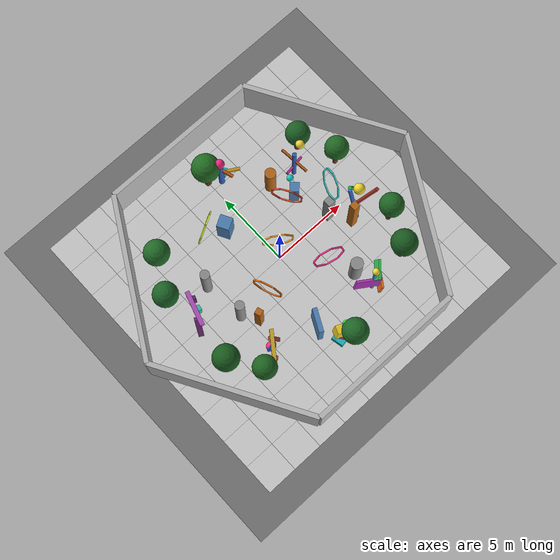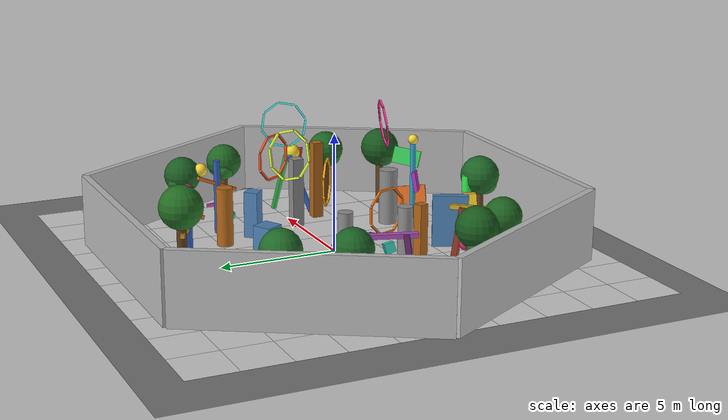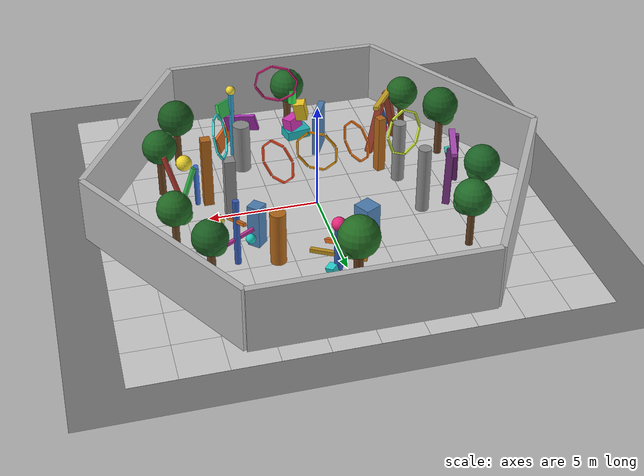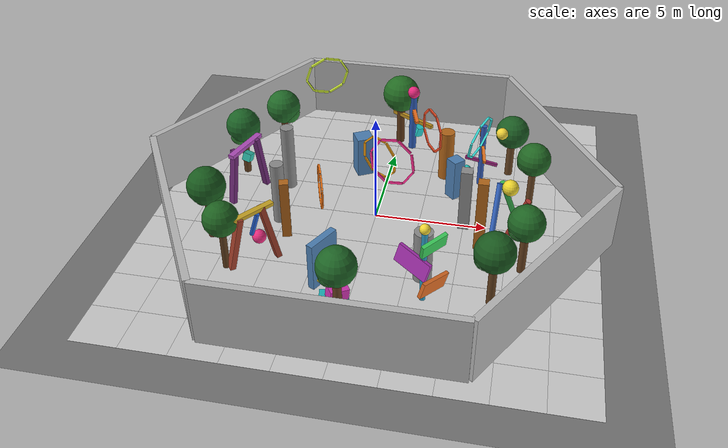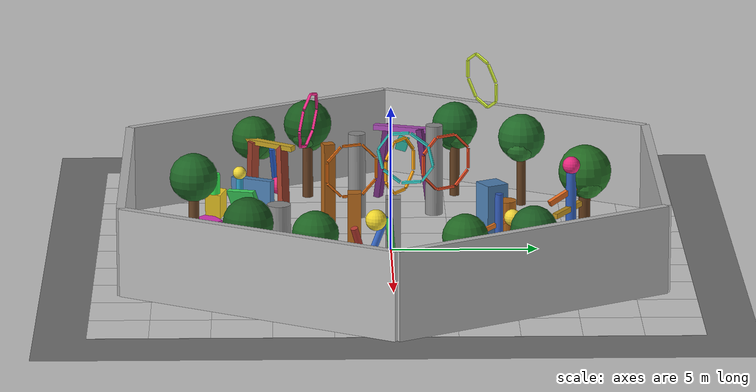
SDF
<?xml version="1.0"?>
<sdf version="1.9">
  <world name="test">
    <physics name="1ms" type="ignored">
      <max_step_size>0.001</max_step_size>
      <real_time_update_rate>1000</real_time_update_rate>
      <real_time_factor>1.0</real_time_factor>
    </physics>

    <plugin filename="gz-sim-physics-system" name="gz::sim::systems::Physics"/>
    <plugin filename="gz-sim-user-commands-system" name="gz::sim::systems::UserCommands"/>
    <plugin filename="gz-sim-scene-broadcaster-system" name="gz::sim::systems::SceneBroadcaster"/>
    <plugin filename="gz-sim-contact-system" name="gz::sim::systems::Contact"/>
    <plugin filename="gz-sim-imu-system" name="gz::sim::systems::Imu"/>
    <plugin filename="gz-sim-air-pressure-system" name="gz::sim::systems::AirPressure"/>
    <plugin filename="gz-sim-navsat-system" name="gz::sim::systems::NavSat"/>
    <plugin filename="gz-sim-sensors-system" name="gz::sim::systems::Sensors">
      <render_engine>ogre2</render_engine>
    </plugin>

    <light type="directional" name="sun">
      <cast_shadows>true</cast_shadows>
      <pose>0 0 10 0 0 0</pose>
      <diffuse>0.8 0.8 0.8 1</diffuse>
      <specular>0.2 0.2 0.2 1</specular>
      <attenuation>
        <range>1000</range>
        <constant>0.9</constant>
        <linear>0.01</linear>
        <quadratic>0.001</quadratic>
      </attenuation>
      <direction>-0.5 0.1 -0.9</direction>
    </light>

    <gravity>0 0 -9.8</gravity>
    <magnetic_field>6e-06 2.3e-05 -4.2e-05</magnetic_field>
    <atmosphere type="adiabatic"/>
    <spherical_coordinates>
      <surface_model>EARTH_WGS84</surface_model>
      <world_frame_orientation>ENU</world_frame_orientation>
      <latitude_deg>0</latitude_deg>
      <longitude_deg>0</longitude_deg>
      <elevation>0</elevation>
      <heading_deg>0</heading_deg>
    </spherical_coordinates>

    <model name="ground_plane">
      <static>true</static>
      <link name="link">
        <collision name="collision">
          <geometry>
            <plane>
              <normal>0 0 1</normal>
              <size>100 100</size>
            </plane>
          </geometry>
        </collision>
        <visual name="visual">
          <geometry>
            <plane>
              <normal>0 0 1</normal>
              <size>100 100</size>
            </plane>
          </geometry>
          <material>
            <lighting>true</lighting>
            <ambient>0.45 0.45 0.45 1</ambient>
            <diffuse>0.45 0.45 0.45 1</diffuse>
            <specular>0.0 0.0 0.0 1</specular>
          </material>
        </visual>
      </link>
    </model>

      <model name="ground_tiles">
        <static>true</static>
        <pose>0 0 0.002 0 0 0</pose>
        <link name="link">
          <visual name="tile_xpm9_ypm9">
            <pose>-9 -9 0 0 0 0</pose>
            <geometry>
              <plane>
                <normal>0 0 1</normal>
                <size>2 2</size>
              </plane>
            </geometry>
            <material>
              <lighting>true</lighting>
              <ambient>0.8 0.8 0.8 1</ambient>
              <diffuse>0.8 0.8 0.8 1</diffuse>
              <specular>0.2 0.2 0.2 1</specular>
              <pbr><metal>
                <albedo_map>model://ground_texture/media/concrete_floor.png</albedo_map>
                <metalness>0.0</metalness>
                <roughness>0.9</roughness>
              </metal></pbr>
            </material>
          </visual>
          <visual name="tile_xpm9_ypm7">
            <pose>-9 -7 0 0 0 0</pose>
            <geometry>
              <plane>
                <normal>0 0 1</normal>
                <size>2 2</size>
              </plane>
            </geometry>
            <material>
              <lighting>true</lighting>
              <ambient>0.8 0.8 0.8 1</ambient>
              <diffuse>0.8 0.8 0.8 1</diffuse>
              <specular>0.2 0.2 0.2 1</specular>
              <pbr><metal>
                <albedo_map>model://ground_texture/media/concrete_floor.png</albedo_map>
                <metalness>0.0</metalness>
                <roughness>0.9</roughness>
              </metal></pbr>
            </material>
          </visual>
          <visual name="tile_xpm9_ypm5">
            <pose>-9 -5 0 0 0 0</pose>
            <geometry>
              <plane>
                <normal>0 0 1</normal>
                <size>2 2</size>
              </plane>
            </geometry>
            <material>
              <lighting>true</lighting>
              <ambient>0.8 0.8 0.8 1</ambient>
              <diffuse>0.8 0.8 0.8 1</diffuse>
              <specular>0.2 0.2 0.2 1</specular>
              <pbr><metal>
                <albedo_map>model://ground_texture/media/concrete_floor.png</albedo_map>
                <metalness>0.0</metalness>
                <roughness>0.9</roughness>
              </metal></pbr>
            </material>
          </visual>
          <visual name="tile_xpm9_ypm3">
            <pose>-9 -3 0 0 0 0</pose>
            <geometry>
              <plane>
                <normal>0 0 1</normal>
                <size>2 2</size>
              </plane>
            </geometry>
            <material>
              <lighting>true</lighting>
              <ambient>0.8 0.8 0.8 1</ambient>
              <diffuse>0.8 0.8 0.8 1</diffuse>
              <specular>0.2 0.2 0.2 1</specular>
              <pbr><metal>
                <albedo_map>model://ground_texture/media/concrete_floor.png</albedo_map>
                <metalness>0.0</metalness>
                <roughness>0.9</roughness>
              </metal></pbr>
            </material>
          </visual>
          <visual name="tile_xpm9_ypm1">
            <pose>-9 -1 0 0 0 0</pose>
            <geometry>
              <plane>
                <normal>0 0 1</normal>
                <size>2 2</size>
              </plane>
            </geometry>
            <material>
              <lighting>true</lighting>
              <ambient>0.8 0.8 0.8 1</ambient>
              <diffuse>0.8 0.8 0.8 1</diffuse>
              <specular>0.2 0.2 0.2 1</specular>
              <pbr><metal>
                <albedo_map>model://ground_texture/media/concrete_floor.png</albedo_map>
                <metalness>0.0</metalness>
                <roughness>0.9</roughness>
              </metal></pbr>
            </material>
          </visual>
          <visual name="tile_xpm9_yp1">
            <pose>-9 1 0 0 0 0</pose>
            <geometry>
              <plane>
                <normal>0 0 1</normal>
                <size>2 2</size>
              </plane>
            </geometry>
            <material>
              <lighting>true</lighting>
              <ambient>0.8 0.8 0.8 1</ambient>
              <diffuse>0.8 0.8 0.8 1</diffuse>
              <specular>0.2 0.2 0.2 1</specular>
              <pbr><metal>
                <albedo_map>model://ground_texture/media/concrete_floor.png</albedo_map>
                <metalness>0.0</metalness>
                <roughness>0.9</roughness>
              </metal></pbr>
            </material>
          </visual>
          <visual name="tile_xpm9_yp3">
            <pose>-9 3 0 0 0 0</pose>
            <geometry>
              <plane>
                <normal>0 0 1</normal>
                <size>2 2</size>
              </plane>
            </geometry>
            <material>
              <lighting>true</lighting>
              <ambient>0.8 0.8 0.8 1</ambient>
              <diffuse>0.8 0.8 0.8 1</diffuse>
              <specular>0.2 0.2 0.2 1</specular>
              <pbr><metal>
                <albedo_map>model://ground_texture/media/concrete_floor.png</albedo_map>
                <metalness>0.0</metalness>
                <roughness>0.9</roughness>
              </metal></pbr>
            </material>
          </visual>
          <visual name="tile_xpm9_yp5">
            <pose>-9 5 0 0 0 0</pose>
            <geometry>
              <plane>
                <normal>0 0 1</normal>
                <size>2 2</size>
              </plane>
            </geometry>
            <material>
              <lighting>true</lighting>
              <ambient>0.8 0.8 0.8 1</ambient>
              <diffuse>0.8 0.8 0.8 1</diffuse>
              <specular>0.2 0.2 0.2 1</specular>
              <pbr><metal>
                <albedo_map>model://ground_texture/media/concrete_floor.png</albedo_map>
                <metalness>0.0</metalness>
                <roughness>0.9</roughness>
              </metal></pbr>
            </material>
          </visual>
          <visual name="tile_xpm9_yp7">
            <pose>-9 7 0 0 0 0</pose>
            <geometry>
              <plane>
                <normal>0 0 1</normal>
                <size>2 2</size>
              </plane>
            </geometry>
            <material>
              <lighting>true</lighting>
              <ambient>0.8 0.8 0.8 1</ambient>
              <diffuse>0.8 0.8 0.8 1</diffuse>
              <specular>0.2 0.2 0.2 1</specular>
              <pbr><metal>
                <albedo_map>model://ground_texture/media/concrete_floor.png</albedo_map>
                <metalness>0.0</metalness>
                <roughness>0.9</roughness>
              </metal></pbr>
            </material>
          </visual>
          <visual name="tile_xpm9_yp9">
            <pose>-9 9 0 0 0 0</pose>
            <geometry>
              <plane>
                <normal>0 0 1</normal>
                <size>2 2</size>
              </plane>
            </geometry>
            <material>
              <lighting>true</lighting>
              <ambient>0.8 0.8 0.8 1</ambient>
              <diffuse>0.8 0.8 0.8 1</diffuse>
              <specular>0.2 0.2 0.2 1</specular>
              <pbr><metal>
                <albedo_map>model://ground_texture/media/concrete_floor.png</albedo_map>
                <metalness>0.0</metalness>
                <roughness>0.9</roughness>
              </metal></pbr>
            </material>
          </visual>
          <visual name="tile_xpm7_ypm9">
            <pose>-7 -9 0 0 0 0</pose>
            <geometry>
              <plane>
                <normal>0 0 1</normal>
                <size>2 2</size>
              </plane>
            </geometry>
            <material>
              <lighting>true</lighting>
              <ambient>0.8 0.8 0.8 1</ambient>
              <diffuse>0.8 0.8 0.8 1</diffuse>
              <specular>0.2 0.2 0.2 1</specular>
              <pbr><metal>
                <albedo_map>model://ground_texture/media/concrete_floor.png</albedo_map>
                <metalness>0.0</metalness>
                <roughness>0.9</roughness>
              </metal></pbr>
            </material>
          </visual>
          <visual name="tile_xpm7_ypm7">
            <pose>-7 -7 0 0 0 0</pose>
            <geometry>
              <plane>
                <normal>0 0 1</normal>
                <size>2 2</size>
              </plane>
            </geometry>
            <material>
              <lighting>true</lighting>
              <ambient>0.8 0.8 0.8 1</ambient>
              <diffuse>0.8 0.8 0.8 1</diffuse>
              <specular>0.2 0.2 0.2 1</specular>
              <pbr><metal>
                <albedo_map>model://ground_texture/media/concrete_floor.png</albedo_map>
                <metalness>0.0</metalness>
                <roughness>0.9</roughness>
              </metal></pbr>
            </material>
          </visual>
          <visual name="tile_xpm7_ypm5">
            <pose>-7 -5 0 0 0 0</pose>
            <geometry>
              <plane>
                <normal>0 0 1</normal>
                <size>2 2</size>
              </plane>
            </geometry>
            <material>
              <lighting>true</lighting>
              <ambient>0.8 0.8 0.8 1</ambient>
              <diffuse>0.8 0.8 0.8 1</diffuse>
              <specular>0.2 0.2 0.2 1</specular>
              <pbr><metal>
                <albedo_map>model://ground_texture/media/concrete_floor.png</albedo_map>
                <metalness>0.0</metalness>
                <roughness>0.9</roughness>
              </metal></pbr>
            </material>
          </visual>
          <visual name="tile_xpm7_ypm3">
            <pose>-7 -3 0 0 0 0</pose>
            <geometry>
              <plane>
                <normal>0 0 1</normal>
                <size>2 2</size>
              </plane>
            </geometry>
            <material>
              <lighting>true</lighting>
              <ambient>0.8 0.8 0.8 1</ambient>
              <diffuse>0.8 0.8 0.8 1</diffuse>
              <specular>0.2 0.2 0.2 1</specular>
              <pbr><metal>
                <albedo_map>model://ground_texture/media/concrete_floor.png</albedo_map>
                <metalness>0.0</metalness>
                <roughness>0.9</roughness>
              </metal></pbr>
            </material>
          </visual>
          <visual name="tile_xpm7_ypm1">
            <pose>-7 -1 0 0 0 0</pose>
            <geometry>
              <plane>
                <normal>0 0 1</normal>
                <size>2 2</size>
              </plane>
            </geometry>
            <material>
              <lighting>true</lighting>
              <ambient>0.8 0.8 0.8 1</ambient>
              <diffuse>0.8 0.8 0.8 1</diffuse>
              <specular>0.2 0.2 0.2 1</specular>
              <pbr><metal>
                <albedo_map>model://ground_texture/media/concrete_floor.png</albedo_map>
                <metalness>0.0</metalness>
                <roughness>0.9</roughness>
              </metal></pbr>
            </material>
          </visual>
          <visual name="tile_xpm7_yp1">
            <pose>-7 1 0 0 0 0</pose>
            <geometry>
              <plane>
                <normal>0 0 1</normal>
                <size>2 2</size>
              </plane>
            </geometry>
            <material>
              <lighting>true</lighting>
              <ambient>0.8 0.8 0.8 1</ambient>
              <diffuse>0.8 0.8 0.8 1</diffuse>
              <specular>0.2 0.2 0.2 1</specular>
              <pbr><metal>
                <albedo_map>model://ground_texture/media/concrete_floor.png</albedo_map>
                <metalness>0.0</metalness>
                <roughness>0.9</roughness>
              </metal></pbr>
            </material>
          </visual>
          <visual name="tile_xpm7_yp3">
            <pose>-7 3 0 0 0 0</pose>
            <geometry>
              <plane>
                <normal>0 0 1</normal>
                <size>2 2</size>
              </plane>
            </geometry>
            <material>
              <lighting>true</lighting>
              <ambient>0.8 0.8 0.8 1</ambient>
              <diffuse>0.8 0.8 0.8 1</diffuse>
              <specular>0.2 0.2 0.2 1</specular>
              <pbr><metal>
                <albedo_map>model://ground_texture/media/concrete_floor.png</albedo_map>
                <metalness>0.0</metalness>
                <roughness>0.9</roughness>
              </metal></pbr>
            </material>
          </visual>
          <visual name="tile_xpm7_yp5">
            <pose>-7 5 0 0 0 0</pose>
            <geometry>
              <plane>
                <normal>0 0 1</normal>
                <size>2 2</size>
              </plane>
            </geometry>
            <material>
              <lighting>true</lighting>
              <ambient>0.8 0.8 0.8 1</ambient>
              <diffuse>0.8 0.8 0.8 1</diffuse>
              <specular>0.2 0.2 0.2 1</specular>
              <pbr><metal>
                <albedo_map>model://ground_texture/media/concrete_floor.png</albedo_map>
                <metalness>0.0</metalness>
                <roughness>0.9</roughness>
              </metal></pbr>
            </material>
          </visual>
          <visual name="tile_xpm7_yp7">
            <pose>-7 7 0 0 0 0</pose>
            <geometry>
              <plane>
                <normal>0 0 1</normal>
                <size>2 2</size>
              </plane>
            </geometry>
            <material>
              <lighting>true</lighting>
              <ambient>0.8 0.8 0.8 1</ambient>
              <diffuse>0.8 0.8 0.8 1</diffuse>
              <specular>0.2 0.2 0.2 1</specular>
              <pbr><metal>
                <albedo_map>model://ground_texture/media/concrete_floor.png</albedo_map>
                <metalness>0.0</metalness>
                <roughness>0.9</roughness>
              </metal></pbr>
            </material>
          </visual>
          <visual name="tile_xpm7_yp9">
            <pose>-7 9 0 0 0 0</pose>
            <geometry>
              <plane>
                <normal>0 0 1</normal>
                <size>2 2</size>
              </plane>
            </geometry>
            <material>
              <lighting>true</lighting>
              <ambient>0.8 0.8 0.8 1</ambient>
              <diffuse>0.8 0.8 0.8 1</diffuse>
              <specular>0.2 0.2 0.2 1</specular>
              <pbr><metal>
                <albedo_map>model://ground_texture/media/concrete_floor.png</albedo_map>
                <metalness>0.0</metalness>
                <roughness>0.9</roughness>
              </metal></pbr>
            </material>
          </visual>
          <visual name="tile_xpm5_ypm9">
            <pose>-5 -9 0 0 0 0</pose>
            <geometry>
              <plane>
                <normal>0 0 1</normal>
                <size>2 2</size>
              </plane>
            </geometry>
            <material>
              <lighting>true</lighting>
              <ambient>0.8 0.8 0.8 1</ambient>
              <diffuse>0.8 0.8 0.8 1</diffuse>
              <specular>0.2 0.2 0.2 1</specular>
              <pbr><metal>
                <albedo_map>model://ground_texture/media/concrete_floor.png</albedo_map>
                <metalness>0.0</metalness>
                <roughness>0.9</roughness>
              </metal></pbr>
            </material>
          </visual>
          <visual name="tile_xpm5_ypm7">
            <pose>-5 -7 0 0 0 0</pose>
            <geometry>
              <plane>
                <normal>0 0 1</normal>
                <size>2 2</size>
              </plane>
            </geometry>
            <material>
              <lighting>true</lighting>
              <ambient>0.8 0.8 0.8 1</ambient>
              <diffuse>0.8 0.8 0.8 1</diffuse>
              <specular>0.2 0.2 0.2 1</specular>
              <pbr><metal>
                <albedo_map>model://ground_texture/media/concrete_floor.png</albedo_map>
                <metalness>0.0</metalness>
                <roughness>0.9</roughness>
              </metal></pbr>
            </material>
          </visual>
          <visual name="tile_xpm5_ypm5">
            <pose>-5 -5 0 0 0 0</pose>
            <geometry>
              <plane>
                <normal>0 0 1</normal>
                <size>2 2</size>
              </plane>
            </geometry>
            <material>
              <lighting>true</lighting>
              <ambient>0.8 0.8 0.8 1</ambient>
              <diffuse>0.8 0.8 0.8 1</diffuse>
              <specular>0.2 0.2 0.2 1</specular>
              <pbr><metal>
                <albedo_map>model://ground_texture/media/concrete_floor.png</albedo_map>
                <metalness>0.0</metalness>
                <roughness>0.9</roughness>
              </metal></pbr>
            </material>
          </visual>
          <visual name="tile_xpm5_ypm3">
            <pose>-5 -3 0 0 0 0</pose>
            <geometry>
              <plane>
                <normal>0 0 1</normal>
                <size>2 2</size>
              </plane>
            </geometry>
            <material>
              <lighting>true</lighting>
              <ambient>0.8 0.8 0.8 1</ambient>
              <diffuse>0.8 0.8 0.8 1</diffuse>
              <specular>0.2 0.2 0.2 1</specular>
              <pbr><metal>
                <albedo_map>model://ground_texture/media/concrete_floor.png</albedo_map>
                <metalness>0.0</metalness>
                <roughness>0.9</roughness>
              </metal></pbr>
            </material>
          </visual>
          <visual name="tile_xpm5_ypm1">
            <pose>-5 -1 0 0 0 0</pose>
            <geometry>
              <plane>
                <normal>0 0 1</normal>
                <size>2 2</size>
              </plane>
            </geometry>
            <material>
              <lighting>true</lighting>
              <ambient>0.8 0.8 0.8 1</ambient>
              <diffuse>0.8 0.8 0.8 1</diffuse>
              <specular>0.2 0.2 0.2 1</specular>
              <pbr><metal>
                <albedo_map>model://ground_texture/media/concrete_floor.png</albedo_map>
                <metalness>0.0</metalness>
                <roughness>0.9</roughness>
              </metal></pbr>
            </material>
          </visual>
          <visual name="tile_xpm5_yp1">
            <pose>-5 1 0 0 0 0</pose>
            <geometry>
              <plane>
                <normal>0 0 1</normal>
                <size>2 2</size>
              </plane>
            </geometry>
            <material>
              <lighting>true</lighting>
              <ambient>0.8 0.8 0.8 1</ambient>
              <diffuse>0.8 0.8 0.8 1</diffuse>
              <specular>0.2 0.2 0.2 1</specular>
              <pbr><metal>
                <albedo_map>model://ground_texture/media/concrete_floor.png</albedo_map>
                <metalness>0.0</metalness>
                <roughness>0.9</roughness>
              </metal></pbr>
            </material>
          </visual>
          <visual name="tile_xpm5_yp3">
            <pose>-5 3 0 0 0 0</pose>
            <geometry>
              <plane>
                <normal>0 0 1</normal>
                <size>2 2</size>
              </plane>
            </geometry>
            <material>
              <lighting>true</lighting>
              <ambient>0.8 0.8 0.8 1</ambient>
              <diffuse>0.8 0.8 0.8 1</diffuse>
              <specular>0.2 0.2 0.2 1</specular>
              <pbr><metal>
                <albedo_map>model://ground_texture/media/concrete_floor.png</albedo_map>
                <metalness>0.0</metalness>
                <roughness>0.9</roughness>
              </metal></pbr>
            </material>
          </visual>
          <visual name="tile_xpm5_yp5">
            <pose>-5 5 0 0 0 0</pose>
            <geometry>
              <plane>
                <normal>0 0 1</normal>
                <size>2 2</size>
              </plane>
            </geometry>
            <material>
              <lighting>true</lighting>
              <ambient>0.8 0.8 0.8 1</ambient>
              <diffuse>0.8 0.8 0.8 1</diffuse>
              <specular>0.2 0.2 0.2 1</specular>
              <pbr><metal>
                <albedo_map>model://ground_texture/media/concrete_floor.png</albedo_map>
                <metalness>0.0</metalness>
                <roughness>0.9</roughness>
              </metal></pbr>
            </material>
          </visual>
          <visual name="tile_xpm5_yp7">
            <pose>-5 7 0 0 0 0</pose>
            <geometry>
              <plane>
                <normal>0 0 1</normal>
                <size>2 2</size>
              </plane>
            </geometry>
            <material>
              <lighting>true</lighting>
              <ambient>0.8 0.8 0.8 1</ambient>
              <diffuse>0.8 0.8 0.8 1</diffuse>
              <specular>0.2 0.2 0.2 1</specular>
              <pbr><metal>
                <albedo_map>model://ground_texture/media/concrete_floor.png</albedo_map>
                <metalness>0.0</metalness>
                <roughness>0.9</roughness>
              </metal></pbr>
            </material>
          </visual>
          <visual name="tile_xpm5_yp9">
            <pose>-5 9 0 0 0 0</pose>
            <geometry>
              <plane>
                <normal>0 0 1</normal>
                <size>2 2</size>
              </plane>
            </geometry>
            <material>
              <lighting>true</lighting>
              <ambient>0.8 0.8 0.8 1</ambient>
              <diffuse>0.8 0.8 0.8 1</diffuse>
              <specular>0.2 0.2 0.2 1</specular>
              <pbr><metal>
                <albedo_map>model://ground_texture/media/concrete_floor.png</albedo_map>
                <metalness>0.0</metalness>
                <roughness>0.9</roughness>
              </metal></pbr>
            </material>
          </visual>
          <visual name="tile_xpm3_ypm9">
            <pose>-3 -9 0 0 0 0</pose>
            <geometry>
              <plane>
                <normal>0 0 1</normal>
                <size>2 2</size>
              </plane>
            </geometry>
            <material>
              <lighting>true</lighting>
              <ambient>0.8 0.8 0.8 1</ambient>
              <diffuse>0.8 0.8 0.8 1</diffuse>
              <specular>0.2 0.2 0.2 1</specular>
              <pbr><metal>
                <albedo_map>model://ground_texture/media/concrete_floor.png</albedo_map>
                <metalness>0.0</metalness>
                <roughness>0.9</roughness>
              </metal></pbr>
            </material>
          </visual>
          <visual name="tile_xpm3_ypm7">
            <pose>-3 -7 0 0 0 0</pose>
            <geometry>
              <plane>
                <normal>0 0 1</normal>
                <size>2 2</size>
              </plane>
            </geometry>
            <material>
              <lighting>true</lighting>
              <ambient>0.8 0.8 0.8 1</ambient>
              <diffuse>0.8 0.8 0.8 1</diffuse>
              <specular>0.2 0.2 0.2 1</specular>
              <pbr><metal>
                <albedo_map>model://ground_texture/media/concrete_floor.png</albedo_map>
                <metalness>0.0</metalness>
                <roughness>0.9</roughness>
              </metal></pbr>
            </material>
          </visual>
          <visual name="tile_xpm3_ypm5">
            <pose>-3 -5 0 0 0 0</pose>
            <geometry>
              <plane>
                <normal>0 0 1</normal>
                <size>2 2</size>
              </plane>
            </geometry>
            <material>
              <lighting>true</lighting>
              <ambient>0.8 0.8 0.8 1</ambient>
              <diffuse>0.8 0.8 0.8 1</diffuse>
              <specular>0.2 0.2 0.2 1</specular>
              <pbr><metal>
                <albedo_map>model://ground_texture/media/concrete_floor.png</albedo_map>
                <metalness>0.0</metalness>
                <roughness>0.9</roughness>
              </metal></pbr>
            </material>
          </visual>
          <visual name="tile_xpm3_ypm3">
            <pose>-3 -3 0 0 0 0</pose>
            <geometry>
              <plane>
                <normal>0 0 1</normal>
                <size>2 2</size>
              </plane>
            </geometry>
            <material>
              <lighting>true</lighting>
              <ambient>0.8 0.8 0.8 1</ambient>
              <diffuse>0.8 0.8 0.8 1</diffuse>
              <specular>0.2 0.2 0.2 1</specular>
              <pbr><metal>
                <albedo_map>model://ground_texture/media/concrete_floor.png</albedo_map>
                <metalness>0.0</metalness>
                <roughness>0.9</roughness>
              </metal></pbr>
            </material>
          </visual>
          <visual name="tile_xpm3_ypm1">
            <pose>-3 -1 0 0 0 0</pose>
            <geometry>
              <plane>
                <normal>0 0 1</normal>
                <size>2 2</size>
              </plane>
            </geometry>
            <material>
              <lighting>true</lighting>
              <ambient>0.8 0.8 0.8 1</ambient>
              <diffuse>0.8 0.8 0.8 1</diffuse>
              <specular>0.2 0.2 0.2 1</specular>
              <pbr><metal>
                <albedo_map>model://ground_texture/media/concrete_floor.png</albedo_map>
                <metalness>0.0</metalness>
                <roughness>0.9</roughness>
              </metal></pbr>
            </material>
          </visual>
          <visual name="tile_xpm3_yp1">
            <pose>-3 1 0 0 0 0</pose>
            <geometry>
              <plane>
                <normal>0 0 1</normal>
                <size>2 2</size>
              </plane>
            </geometry>
            <material>
              <lighting>true</lighting>
              <ambient>0.8 0.8 0.8 1</ambient>
              <diffuse>0.8 0.8 0.8 1</diffuse>
              <specular>0.2 0.2 0.2 1</specular>
              <pbr><metal>
                <albedo_map>model://ground_texture/media/concrete_floor.png</albedo_map>
                <metalness>0.0</metalness>
                <roughness>0.9</roughness>
              </metal></pbr>
            </material>
          </visual>
          <visual name="tile_xpm3_yp3">
            <pose>-3 3 0 0 0 0</pose>
            <geometry>
              <plane>
                <normal>0 0 1</normal>
                <size>2 2</size>
              </plane>
            </geometry>
            <material>
              <lighting>true</lighting>
              <ambient>0.8 0.8 0.8 1</ambient>
              <diffuse>0.8 0.8 0.8 1</diffuse>
              <specular>0.2 0.2 0.2 1</specular>
              <pbr><metal>
                <albedo_map>model://ground_texture/media/concrete_floor.png</albedo_map>
                <metalness>0.0</metalness>
                <roughness>0.9</roughness>
              </metal></pbr>
            </material>
          </visual>
          <visual name="tile_xpm3_yp5">
            <pose>-3 5 0 0 0 0</pose>
            <geometry>
              <plane>
                <normal>0 0 1</normal>
                <size>2 2</size>
              </plane>
            </geometry>
            <material>
              <lighting>true</lighting>
              <ambient>0.8 0.8 0.8 1</ambient>
              <diffuse>0.8 0.8 0.8 1</diffuse>
              <specular>0.2 0.2 0.2 1</specular>
              <pbr><metal>
                <albedo_map>model://ground_texture/media/concrete_floor.png</albedo_map>
                <metalness>0.0</metalness>
                <roughness>0.9</roughness>
              </metal></pbr>
            </material>
          </visual>
          <visual name="tile_xpm3_yp7">
            <pose>-3 7 0 0 0 0</pose>
            <geometry>
              <plane>
                <normal>0 0 1</normal>
                <size>2 2</size>
              </plane>
            </geometry>
            <material>
              <lighting>true</lighting>
              <ambient>0.8 0.8 0.8 1</ambient>
              <diffuse>0.8 0.8 0.8 1</diffuse>
              <specular>0.2 0.2 0.2 1</specular>
              <pbr><metal>
                <albedo_map>model://ground_texture/media/concrete_floor.png</albedo_map>
                <metalness>0.0</metalness>
                <roughness>0.9</roughness>
              </metal></pbr>
            </material>
          </visual>
          <visual name="tile_xpm3_yp9">
            <pose>-3 9 0 0 0 0</pose>
            <geometry>
              <plane>
                <normal>0 0 1</normal>
                <size>2 2</size>
              </plane>
            </geometry>
            <material>
              <lighting>true</lighting>
              <ambient>0.8 0.8 0.8 1</ambient>
              <diffuse>0.8 0.8 0.8 1</diffuse>
              <specular>0.2 0.2 0.2 1</specular>
              <pbr><metal>
                <albedo_map>model://ground_texture/media/concrete_floor.png</albedo_map>
                <metalness>0.0</metalness>
                <roughness>0.9</roughness>
              </metal></pbr>
            </material>
          </visual>
          <visual name="tile_xpm1_ypm9">
            <pose>-1 -9 0 0 0 0</pose>
            <geometry>
              <plane>
                <normal>0 0 1</normal>
                <size>2 2</size>
              </plane>
            </geometry>
            <material>
              <lighting>true</lighting>
              <ambient>0.8 0.8 0.8 1</ambient>
              <diffuse>0.8 0.8 0.8 1</diffuse>
              <specular>0.2 0.2 0.2 1</specular>
              <pbr><metal>
                <albedo_map>model://ground_texture/media/concrete_floor.png</albedo_map>
                <metalness>0.0</metalness>
                <roughness>0.9</roughness>
              </metal></pbr>
            </material>
          </visual>
          <visual name="tile_xpm1_ypm7">
            <pose>-1 -7 0 0 0 0</pose>
            <geometry>
              <plane>
                <normal>0 0 1</normal>
                <size>2 2</size>
              </plane>
            </geometry>
            <material>
              <lighting>true</lighting>
              <ambient>0.8 0.8 0.8 1</ambient>
              <diffuse>0.8 0.8 0.8 1</diffuse>
              <specular>0.2 0.2 0.2 1</specular>
              <pbr><metal>
                <albedo_map>model://ground_texture/media/concrete_floor.png</albedo_map>
                <metalness>0.0</metalness>
                <roughness>0.9</roughness>
              </metal></pbr>
            </material>
          </visual>
          <visual name="tile_xpm1_ypm5">
            <pose>-1 -5 0 0 0 0</pose>
            <geometry>
              <plane>
                <normal>0 0 1</normal>
                <size>2 2</size>
              </plane>
            </geometry>
            <material>
              <lighting>true</lighting>
              <ambient>0.8 0.8 0.8 1</ambient>
              <diffuse>0.8 0.8 0.8 1</diffuse>
              <specular>0.2 0.2 0.2 1</specular>
              <pbr><metal>
                <albedo_map>model://ground_texture/media/concrete_floor.png</albedo_map>
                <metalness>0.0</metalness>
                <roughness>0.9</roughness>
              </metal></pbr>
            </material>
          </visual>
          <visual name="tile_xpm1_ypm3">
            <pose>-1 -3 0 0 0 0</pose>
            <geometry>
              <plane>
                <normal>0 0 1</normal>
                <size>2 2</size>
              </plane>
            </geometry>
            <material>
              <lighting>true</lighting>
              <ambient>0.8 0.8 0.8 1</ambient>
              <diffuse>0.8 0.8 0.8 1</diffuse>
              <specular>0.2 0.2 0.2 1</specular>
              <pbr><metal>
                <albedo_map>model://ground_texture/media/concrete_floor.png</albedo_map>
                <metalness>0.0</metalness>
                <roughness>0.9</roughness>
              </metal></pbr>
            </material>
          </visual>
          <visual name="tile_xpm1_ypm1">
            <pose>-1 -1 0 0 0 0</pose>
            <geometry>
              <plane>
                <normal>0 0 1</normal>
                <size>2 2</size>
              </plane>
            </geometry>
            <material>
              <lighting>true</lighting>
              <ambient>0.8 0.8 0.8 1</ambient>
              <diffuse>0.8 0.8 0.8 1</diffuse>
              <specular>0.2 0.2 0.2 1</specular>
              <pbr><metal>
                <albedo_map>model://ground_texture/media/concrete_floor.png</albedo_map>
                <metalness>0.0</metalness>
                <roughness>0.9</roughness>
              </metal></pbr>
            </material>
          </visual>
          <visual name="tile_xpm1_yp1">
            <pose>-1 1 0 0 0 0</pose>
            <geometry>
              <plane>
                <normal>0 0 1</normal>
                <size>2 2</size>
              </plane>
            </geometry>
            <material>
              <lighting>true</lighting>
              <ambient>0.8 0.8 0.8 1</ambient>
              <diffuse>0.8 0.8 0.8 1</diffuse>
              <specular>0.2 0.2 0.2 1</specular>
              <pbr><metal>
                <albedo_map>model://ground_texture/media/concrete_floor.png</albedo_map>
                <metalness>0.0</metalness>
                <roughness>0.9</roughness>
              </metal></pbr>
            </material>
          </visual>
          <visual name="tile_xpm1_yp3">
            <pose>-1 3 0 0 0 0</pose>
            <geometry>
              <plane>
                <normal>0 0 1</normal>
                <size>2 2</size>
              </plane>
            </geometry>
            <material>
              <lighting>true</lighting>
              <ambient>0.8 0.8 0.8 1</ambient>
              <diffuse>0.8 0.8 0.8 1</diffuse>
              <specular>0.2 0.2 0.2 1</specular>
              <pbr><metal>
                <albedo_map>model://ground_texture/media/concrete_floor.png</albedo_map>
                <metalness>0.0</metalness>
                <roughness>0.9</roughness>
              </metal></pbr>
            </material>
          </visual>
          <visual name="tile_xpm1_yp5">
            <pose>-1 5 0 0 0 0</pose>
            <geometry>
              <plane>
                <normal>0 0 1</normal>
                <size>2 2</size>
              </plane>
            </geometry>
            <material>
              <lighting>true</lighting>
              <ambient>0.8 0.8 0.8 1</ambient>
              <diffuse>0.8 0.8 0.8 1</diffuse>
              <specular>0.2 0.2 0.2 1</specular>
              <pbr><metal>
                <albedo_map>model://ground_texture/media/concrete_floor.png</albedo_map>
                <metalness>0.0</metalness>
                <roughness>0.9</roughness>
              </metal></pbr>
            </material>
          </visual>
          <visual name="tile_xpm1_yp7">
            <pose>-1 7 0 0 0 0</pose>
            <geometry>
              <plane>
                <normal>0 0 1</normal>
                <size>2 2</size>
              </plane>
            </geometry>
            <material>
              <lighting>true</lighting>
              <ambient>0.8 0.8 0.8 1</ambient>
              <diffuse>0.8 0.8 0.8 1</diffuse>
              <specular>0.2 0.2 0.2 1</specular>
              <pbr><metal>
                <albedo_map>model://ground_texture/media/concrete_floor.png</albedo_map>
                <metalness>0.0</metalness>
                <roughness>0.9</roughness>
              </metal></pbr>
            </material>
          </visual>
          <visual name="tile_xpm1_yp9">
            <pose>-1 9 0 0 0 0</pose>
            <geometry>
              <plane>
                <normal>0 0 1</normal>
                <size>2 2</size>
              </plane>
            </geometry>
            <material>
              <lighting>true</lighting>
              <ambient>0.8 0.8 0.8 1</ambient>
              <diffuse>0.8 0.8 0.8 1</diffuse>
              <specular>0.2 0.2 0.2 1</specular>
              <pbr><metal>
                <albedo_map>model://ground_texture/media/concrete_floor.png</albedo_map>
                <metalness>0.0</metalness>
                <roughness>0.9</roughness>
              </metal></pbr>
            </material>
          </visual>
          <visual name="tile_xp1_ypm9">
            <pose>1 -9 0 0 0 0</pose>
            <geometry>
              <plane>
                <normal>0 0 1</normal>
                <size>2 2</size>
              </plane>
            </geometry>
            <material>
              <lighting>true</lighting>
              <ambient>0.8 0.8 0.8 1</ambient>
              <diffuse>0.8 0.8 0.8 1</diffuse>
              <specular>0.2 0.2 0.2 1</specular>
              <pbr><metal>
                <albedo_map>model://ground_texture/media/concrete_floor.png</albedo_map>
                <metalness>0.0</metalness>
                <roughness>0.9</roughness>
              </metal></pbr>
            </material>
          </visual>
          <visual name="tile_xp1_ypm7">
            <pose>1 -7 0 0 0 0</pose>
            <geometry>
              <plane>
                <normal>0 0 1</normal>
                <size>2 2</size>
              </plane>
            </geometry>
            <material>
              <lighting>true</lighting>
              <ambient>0.8 0.8 0.8 1</ambient>
              <diffuse>0.8 0.8 0.8 1</diffuse>
              <specular>0.2 0.2 0.2 1</specular>
              <pbr><metal>
                <albedo_map>model://ground_texture/media/concrete_floor.png</albedo_map>
                <metalness>0.0</metalness>
                <roughness>0.9</roughness>
              </metal></pbr>
            </material>
          </visual>
          <visual name="tile_xp1_ypm5">
            <pose>1 -5 0 0 0 0</pose>
            <geometry>
              <plane>
                <normal>0 0 1</normal>
                <size>2 2</size>
              </plane>
            </geometry>
            <material>
              <lighting>true</lighting>
              <ambient>0.8 0.8 0.8 1</ambient>
              <diffuse>0.8 0.8 0.8 1</diffuse>
              <specular>0.2 0.2 0.2 1</specular>
              <pbr><metal>
                <albedo_map>model://ground_texture/media/concrete_floor.png</albedo_map>
                <metalness>0.0</metalness>
                <roughness>0.9</roughness>
              </metal></pbr>
            </material>
          </visual>
          <visual name="tile_xp1_ypm3">
            <pose>1 -3 0 0 0 0</pose>
            <geometry>
              <plane>
                <normal>0 0 1</normal>
                <size>2 2</size>
              </plane>
            </geometry>
            <material>
              <lighting>true</lighting>
              <ambient>0.8 0.8 0.8 1</ambient>
              <diffuse>0.8 0.8 0.8 1</diffuse>
              <specular>0.2 0.2 0.2 1</specular>
              <pbr><metal>
                <albedo_map>model://ground_texture/media/concrete_floor.png</albedo_map>
                <metalness>0.0</metalness>
                <roughness>0.9</roughness>
              </metal></pbr>
            </material>
          </visual>
          <visual name="tile_xp1_ypm1">
            <pose>1 -1 0 0 0 0</pose>
            <geometry>
              <plane>
                <normal>0 0 1</normal>
                <size>2 2</size>
              </plane>
            </geometry>
            <material>
              <lighting>true</lighting>
              <ambient>0.8 0.8 0.8 1</ambient>
              <diffuse>0.8 0.8 0.8 1</diffuse>
              <specular>0.2 0.2 0.2 1</specular>
              <pbr><metal>
                <albedo_map>model://ground_texture/media/concrete_floor.png</albedo_map>
                <metalness>0.0</metalness>
                <roughness>0.9</roughness>
              </metal></pbr>
            </material>
          </visual>
          <visual name="tile_xp1_yp1">
            <pose>1 1 0 0 0 0</pose>
            <geometry>
              <plane>
                <normal>0 0 1</normal>
                <size>2 2</size>
              </plane>
            </geometry>
            <material>
              <lighting>true</lighting>
              <ambient>0.8 0.8 0.8 1</ambient>
              <diffuse>0.8 0.8 0.8 1</diffuse>
              <specular>0.2 0.2 0.2 1</specular>
              <pbr><metal>
                <albedo_map>model://ground_texture/media/concrete_floor.png</albedo_map>
                <metalness>0.0</metalness>
                <roughness>0.9</roughness>
              </metal></pbr>
            </material>
          </visual>
          <visual name="tile_xp1_yp3">
            <pose>1 3 0 0 0 0</pose>
            <geometry>
              <plane>
                <normal>0 0 1</normal>
                <size>2 2</size>
              </plane>
            </geometry>
            <material>
              <lighting>true</lighting>
              <ambient>0.8 0.8 0.8 1</ambient>
              <diffuse>0.8 0.8 0.8 1</diffuse>
              <specular>0.2 0.2 0.2 1</specular>
              <pbr><metal>
                <albedo_map>model://ground_texture/media/concrete_floor.png</albedo_map>
                <metalness>0.0</metalness>
                <roughness>0.9</roughness>
              </metal></pbr>
            </material>
          </visual>
          <visual name="tile_xp1_yp5">
            <pose>1 5 0 0 0 0</pose>
            <geometry>
              <plane>
                <normal>0 0 1</normal>
                <size>2 2</size>
              </plane>
            </geometry>
            <material>
              <lighting>true</lighting>
              <ambient>0.8 0.8 0.8 1</ambient>
              <diffuse>0.8 0.8 0.8 1</diffuse>
              <specular>0.2 0.2 0.2 1</specular>
              <pbr><metal>
                <albedo_map>model://ground_texture/media/concrete_floor.png</albedo_map>
                <metalness>0.0</metalness>
                <roughness>0.9</roughness>
              </metal></pbr>
            </material>
          </visual>
          <visual name="tile_xp1_yp7">
            <pose>1 7 0 0 0 0</pose>
            <geometry>
              <plane>
                <normal>0 0 1</normal>
                <size>2 2</size>
              </plane>
            </geometry>
            <material>
              <lighting>true</lighting>
              <ambient>0.8 0.8 0.8 1</ambient>
              <diffuse>0.8 0.8 0.8 1</diffuse>
              <specular>0.2 0.2 0.2 1</specular>
              <pbr><metal>
                <albedo_map>model://ground_texture/media/concrete_floor.png</albedo_map>
                <metalness>0.0</metalness>
                <roughness>0.9</roughness>
              </metal></pbr>
            </material>
          </visual>
          <visual name="tile_xp1_yp9">
            <pose>1 9 0 0 0 0</pose>
            <geometry>
              <plane>
                <normal>0 0 1</normal>
                <size>2 2</size>
              </plane>
            </geometry>
            <material>
              <lighting>true</lighting>
              <ambient>0.8 0.8 0.8 1</ambient>
              <diffuse>0.8 0.8 0.8 1</diffuse>
              <specular>0.2 0.2 0.2 1</specular>
              <pbr><metal>
                <albedo_map>model://ground_texture/media/concrete_floor.png</albedo_map>
                <metalness>0.0</metalness>
                <roughness>0.9</roughness>
              </metal></pbr>
            </material>
          </visual>
          <visual name="tile_xp3_ypm9">
            <pose>3 -9 0 0 0 0</pose>
            <geometry>
              <plane>
                <normal>0 0 1</normal>
                <size>2 2</size>
              </plane>
            </geometry>
            <material>
              <lighting>true</lighting>
              <ambient>0.8 0.8 0.8 1</ambient>
              <diffuse>0.8 0.8 0.8 1</diffuse>
              <specular>0.2 0.2 0.2 1</specular>
              <pbr><metal>
                <albedo_map>model://ground_texture/media/concrete_floor.png</albedo_map>
                <metalness>0.0</metalness>
                <roughness>0.9</roughness>
              </metal></pbr>
            </material>
          </visual>
          <visual name="tile_xp3_ypm7">
            <pose>3 -7 0 0 0 0</pose>
            <geometry>
              <plane>
                <normal>0 0 1</normal>
                <size>2 2</size>
              </plane>
            </geometry>
            <material>
              <lighting>true</lighting>
              <ambient>0.8 0.8 0.8 1</ambient>
              <diffuse>0.8 0.8 0.8 1</diffuse>
              <specular>0.2 0.2 0.2 1</specular>
              <pbr><metal>
                <albedo_map>model://ground_texture/media/concrete_floor.png</albedo_map>
                <metalness>0.0</metalness>
                <roughness>0.9</roughness>
              </metal></pbr>
            </material>
          </visual>
          <visual name="tile_xp3_ypm5">
            <pose>3 -5 0 0 0 0</pose>
            <geometry>
              <plane>
                <normal>0 0 1</normal>
                <size>2 2</size>
              </plane>
            </geometry>
            <material>
              <lighting>true</lighting>
              <ambient>0.8 0.8 0.8 1</ambient>
              <diffuse>0.8 0.8 0.8 1</diffuse>
              <specular>0.2 0.2 0.2 1</specular>
              <pbr><metal>
                <albedo_map>model://ground_texture/media/concrete_floor.png</albedo_map>
                <metalness>0.0</metalness>
                <roughness>0.9</roughness>
              </metal></pbr>
            </material>
          </visual>
          <visual name="tile_xp3_ypm3">
            <pose>3 -3 0 0 0 0</pose>
            <geometry>
              <plane>
                <normal>0 0 1</normal>
                <size>2 2</size>
              </plane>
            </geometry>
            <material>
              <lighting>true</lighting>
              <ambient>0.8 0.8 0.8 1</ambient>
              <diffuse>0.8 0.8 0.8 1</diffuse>
              <specular>0.2 0.2 0.2 1</specular>
              <pbr><metal>
                <albedo_map>model://ground_texture/media/concrete_floor.png</albedo_map>
                <metalness>0.0</metalness>
                <roughness>0.9</roughness>
              </metal></pbr>
            </material>
          </visual>
          <visual name="tile_xp3_ypm1">
            <pose>3 -1 0 0 0 0</pose>
            <geometry>
              <plane>
                <normal>0 0 1</normal>
                <size>2 2</size>
              </plane>
            </geometry>
            <material>
              <lighting>true</lighting>
              <ambient>0.8 0.8 0.8 1</ambient>
              <diffuse>0.8 0.8 0.8 1</diffuse>
              <specular>0.2 0.2 0.2 1</specular>
              <pbr><metal>
                <albedo_map>model://ground_texture/media/concrete_floor.png</albedo_map>
                <metalness>0.0</metalness>
                <roughness>0.9</roughness>
              </metal></pbr>
            </material>
          </visual>
          <visual name="tile_xp3_yp1">
            <pose>3 1 0 0 0 0</pose>
            <geometry>
              <plane>
                <normal>0 0 1</normal>
                <size>2 2</size>
              </plane>
            </geometry>
            <material>
              <lighting>true</lighting>
              <ambient>0.8 0.8 0.8 1</ambient>
              <diffuse>0.8 0.8 0.8 1</diffuse>
              <specular>0.2 0.2 0.2 1</specular>
              <pbr><metal>
                <albedo_map>model://ground_texture/media/concrete_floor.png</albedo_map>
                <metalness>0.0</metalness>
                <roughness>0.9</roughness>
              </metal></pbr>
            </material>
          </visual>
          <visual name="tile_xp3_yp3">
            <pose>3 3 0 0 0 0</pose>
            <geometry>
              <plane>
                <normal>0 0 1</normal>
                <size>2 2</size>
              </plane>
            </geometry>
            <material>
              <lighting>true</lighting>
              <ambient>0.8 0.8 0.8 1</ambient>
              <diffuse>0.8 0.8 0.8 1</diffuse>
              <specular>0.2 0.2 0.2 1</specular>
              <pbr><metal>
                <albedo_map>model://ground_texture/media/concrete_floor.png</albedo_map>
                <metalness>0.0</metalness>
                <roughness>0.9</roughness>
              </metal></pbr>
            </material>
          </visual>
          <visual name="tile_xp3_yp5">
            <pose>3 5 0 0 0 0</pose>
            <geometry>
              <plane>
                <normal>0 0 1</normal>
                <size>2 2</size>
              </plane>
            </geometry>
            <material>
              <lighting>true</lighting>
              <ambient>0.8 0.8 0.8 1</ambient>
              <diffuse>0.8 0.8 0.8 1</diffuse>
              <specular>0.2 0.2 0.2 1</specular>
              <pbr><metal>
                <albedo_map>model://ground_texture/media/concrete_floor.png</albedo_map>
                <metalness>0.0</metalness>
                <roughness>0.9</roughness>
              </metal></pbr>
            </material>
          </visual>
          <visual name="tile_xp3_yp7">
            <pose>3 7 0 0 0 0</pose>
            <geometry>
              <plane>
                <normal>0 0 1</normal>
                <size>2 2</size>
              </plane>
            </geometry>
            <material>
              <lighting>true</lighting>
              <ambient>0.8 0.8 0.8 1</ambient>
              <diffuse>0.8 0.8 0.8 1</diffuse>
              <specular>0.2 0.2 0.2 1</specular>
              <pbr><metal>
                <albedo_map>model://ground_texture/media/concrete_floor.png</albedo_map>
                <metalness>0.0</metalness>
                <roughness>0.9</roughness>
              </metal></pbr>
            </material>
          </visual>
          <visual name="tile_xp3_yp9">
            <pose>3 9 0 0 0 0</pose>
            <geometry>
              <plane>
                <normal>0 0 1</normal>
                <size>2 2</size>
              </plane>
            </geometry>
            <material>
              <lighting>true</lighting>
              <ambient>0.8 0.8 0.8 1</ambient>
              <diffuse>0.8 0.8 0.8 1</diffuse>
              <specular>0.2 0.2 0.2 1</specular>
              <pbr><metal>
                <albedo_map>model://ground_texture/media/concrete_floor.png</albedo_map>
                <metalness>0.0</metalness>
                <roughness>0.9</roughness>
              </metal></pbr>
            </material>
          </visual>
          <visual name="tile_xp5_ypm9">
            <pose>5 -9 0 0 0 0</pose>
            <geometry>
              <plane>
                <normal>0 0 1</normal>
                <size>2 2</size>
              </plane>
            </geometry>
            <material>
              <lighting>true</lighting>
              <ambient>0.8 0.8 0.8 1</ambient>
              <diffuse>0.8 0.8 0.8 1</diffuse>
              <specular>0.2 0.2 0.2 1</specular>
              <pbr><metal>
                <albedo_map>model://ground_texture/media/concrete_floor.png</albedo_map>
                <metalness>0.0</metalness>
                <roughness>0.9</roughness>
              </metal></pbr>
            </material>
          </visual>
          <visual name="tile_xp5_ypm7">
            <pose>5 -7 0 0 0 0</pose>
            <geometry>
              <plane>
                <normal>0 0 1</normal>
                <size>2 2</size>
              </plane>
            </geometry>
            <material>
              <lighting>true</lighting>
              <ambient>0.8 0.8 0.8 1</ambient>
              <diffuse>0.8 0.8 0.8 1</diffuse>
              <specular>0.2 0.2 0.2 1</specular>
              <pbr><metal>
                <albedo_map>model://ground_texture/media/concrete_floor.png</albedo_map>
                <metalness>0.0</metalness>
                <roughness>0.9</roughness>
              </metal></pbr>
            </material>
          </visual>
          <visual name="tile_xp5_ypm5">
            <pose>5 -5 0 0 0 0</pose>
            <geometry>
              <plane>
                <normal>0 0 1</normal>
                <size>2 2</size>
              </plane>
            </geometry>
            <material>
              <lighting>true</lighting>
              <ambient>0.8 0.8 0.8 1</ambient>
              <diffuse>0.8 0.8 0.8 1</diffuse>
              <specular>0.2 0.2 0.2 1</specular>
              <pbr><metal>
                <albedo_map>model://ground_texture/media/concrete_floor.png</albedo_map>
                <metalness>0.0</metalness>
                <roughness>0.9</roughness>
              </metal></pbr>
            </material>
          </visual>
          <visual name="tile_xp5_ypm3">
            <pose>5 -3 0 0 0 0</pose>
            <geometry>
              <plane>
                <normal>0 0 1</normal>
                <size>2 2</size>
              </plane>
            </geometry>
            <material>
              <lighting>true</lighting>
              <ambient>0.8 0.8 0.8 1</ambient>
              <diffuse>0.8 0.8 0.8 1</diffuse>
              <specular>0.2 0.2 0.2 1</specular>
              <pbr><metal>
                <albedo_map>model://ground_texture/media/concrete_floor.png</albedo_map>
                <metalness>0.0</metalness>
                <roughness>0.9</roughness>
              </metal></pbr>
            </material>
          </visual>
          <visual name="tile_xp5_ypm1">
            <pose>5 -1 0 0 0 0</pose>
            <geometry>
              <plane>
                <normal>0 0 1</normal>
                <size>2 2</size>
              </plane>
            </geometry>
            <material>
              <lighting>true</lighting>
              <ambient>0.8 0.8 0.8 1</ambient>
              <diffuse>0.8 0.8 0.8 1</diffuse>
              <specular>0.2 0.2 0.2 1</specular>
              <pbr><metal>
                <albedo_map>model://ground_texture/media/concrete_floor.png</albedo_map>
                <metalness>0.0</metalness>
                <roughness>0.9</roughness>
              </metal></pbr>
            </material>
          </visual>
          <visual name="tile_xp5_yp1">
            <pose>5 1 0 0 0 0</pose>
            <geometry>
              <plane>
                <normal>0 0 1</normal>
                <size>2 2</size>
              </plane>
            </geometry>
            <material>
              <lighting>true</lighting>
              <ambient>0.8 0.8 0.8 1</ambient>
              <diffuse>0.8 0.8 0.8 1</diffuse>
              <specular>0.2 0.2 0.2 1</specular>
              <pbr><metal>
                <albedo_map>model://ground_texture/media/concrete_floor.png</albedo_map>
                <metalness>0.0</metalness>
                <roughness>0.9</roughness>
              </metal></pbr>
            </material>
          </visual>
          <visual name="tile_xp5_yp3">
            <pose>5 3 0 0 0 0</pose>
            <geometry>
              <plane>
                <normal>0 0 1</normal>
                <size>2 2</size>
              </plane>
            </geometry>
            <material>
              <lighting>true</lighting>
              <ambient>0.8 0.8 0.8 1</ambient>
              <diffuse>0.8 0.8 0.8 1</diffuse>
              <specular>0.2 0.2 0.2 1</specular>
              <pbr><metal>
                <albedo_map>model://ground_texture/media/concrete_floor.png</albedo_map>
                <metalness>0.0</metalness>
                <roughness>0.9</roughness>
              </metal></pbr>
            </material>
          </visual>
          <visual name="tile_xp5_yp5">
            <pose>5 5 0 0 0 0</pose>
            <geometry>
              <plane>
                <normal>0 0 1</normal>
                <size>2 2</size>
              </plane>
            </geometry>
            <material>
              <lighting>true</lighting>
              <ambient>0.8 0.8 0.8 1</ambient>
              <diffuse>0.8 0.8 0.8 1</diffuse>
              <specular>0.2 0.2 0.2 1</specular>
              <pbr><metal>
                <albedo_map>model://ground_texture/media/concrete_floor.png</albedo_map>
                <metalness>0.0</metalness>
                <roughness>0.9</roughness>
              </metal></pbr>
            </material>
          </visual>
          <visual name="tile_xp5_yp7">
            <pose>5 7 0 0 0 0</pose>
            <geometry>
              <plane>
                <normal>0 0 1</normal>
                <size>2 2</size>
              </plane>
            </geometry>
            <material>
              <lighting>true</lighting>
              <ambient>0.8 0.8 0.8 1</ambient>
              <diffuse>0.8 0.8 0.8 1</diffuse>
              <specular>0.2 0.2 0.2 1</specular>
              <pbr><metal>
                <albedo_map>model://ground_texture/media/concrete_floor.png</albedo_map>
                <metalness>0.0</metalness>
                <roughness>0.9</roughness>
              </metal></pbr>
            </material>
          </visual>
          <visual name="tile_xp5_yp9">
            <pose>5 9 0 0 0 0</pose>
            <geometry>
              <plane>
                <normal>0 0 1</normal>
                <size>2 2</size>
              </plane>
            </geometry>
            <material>
              <lighting>true</lighting>
              <ambient>0.8 0.8 0.8 1</ambient>
              <diffuse>0.8 0.8 0.8 1</diffuse>
              <specular>0.2 0.2 0.2 1</specular>
              <pbr><metal>
                <albedo_map>model://ground_texture/media/concrete_floor.png</albedo_map>
                <metalness>0.0</metalness>
                <roughness>0.9</roughness>
              </metal></pbr>
            </material>
          </visual>
          <visual name="tile_xp7_ypm9">
            <pose>7 -9 0 0 0 0</pose>
            <geometry>
              <plane>
                <normal>0 0 1</normal>
                <size>2 2</size>
              </plane>
            </geometry>
            <material>
              <lighting>true</lighting>
              <ambient>0.8 0.8 0.8 1</ambient>
              <diffuse>0.8 0.8 0.8 1</diffuse>
              <specular>0.2 0.2 0.2 1</specular>
              <pbr><metal>
                <albedo_map>model://ground_texture/media/concrete_floor.png</albedo_map>
                <metalness>0.0</metalness>
                <roughness>0.9</roughness>
              </metal></pbr>
            </material>
          </visual>
          <visual name="tile_xp7_ypm7">
            <pose>7 -7 0 0 0 0</pose>
            <geometry>
              <plane>
                <normal>0 0 1</normal>
                <size>2 2</size>
              </plane>
            </geometry>
            <material>
              <lighting>true</lighting>
              <ambient>0.8 0.8 0.8 1</ambient>
              <diffuse>0.8 0.8 0.8 1</diffuse>
              <specular>0.2 0.2 0.2 1</specular>
              <pbr><metal>
                <albedo_map>model://ground_texture/media/concrete_floor.png</albedo_map>
                <metalness>0.0</metalness>
                <roughness>0.9</roughness>
              </metal></pbr>
            </material>
          </visual>
          <visual name="tile_xp7_ypm5">
            <pose>7 -5 0 0 0 0</pose>
            <geometry>
              <plane>
                <normal>0 0 1</normal>
                <size>2 2</size>
              </plane>
            </geometry>
            <material>
              <lighting>true</lighting>
              <ambient>0.8 0.8 0.8 1</ambient>
              <diffuse>0.8 0.8 0.8 1</diffuse>
              <specular>0.2 0.2 0.2 1</specular>
              <pbr><metal>
                <albedo_map>model://ground_texture/media/concrete_floor.png</albedo_map>
                <metalness>0.0</metalness>
                <roughness>0.9</roughness>
              </metal></pbr>
            </material>
          </visual>
          <visual name="tile_xp7_ypm3">
            <pose>7 -3 0 0 0 0</pose>
            <geometry>
              <plane>
                <normal>0 0 1</normal>
                <size>2 2</size>
              </plane>
            </geometry>
            <material>
              <lighting>true</lighting>
              <ambient>0.8 0.8 0.8 1</ambient>
              <diffuse>0.8 0.8 0.8 1</diffuse>
              <specular>0.2 0.2 0.2 1</specular>
              <pbr><metal>
                <albedo_map>model://ground_texture/media/concrete_floor.png</albedo_map>
                <metalness>0.0</metalness>
                <roughness>0.9</roughness>
              </metal></pbr>
            </material>
          </visual>
          <visual name="tile_xp7_ypm1">
            <pose>7 -1 0 0 0 0</pose>
            <geometry>
              <plane>
                <normal>0 0 1</normal>
                <size>2 2</size>
              </plane>
            </geometry>
            <material>
              <lighting>true</lighting>
              <ambient>0.8 0.8 0.8 1</ambient>
              <diffuse>0.8 0.8 0.8 1</diffuse>
              <specular>0.2 0.2 0.2 1</specular>
              <pbr><metal>
                <albedo_map>model://ground_texture/media/concrete_floor.png</albedo_map>
                <metalness>0.0</metalness>
                <roughness>0.9</roughness>
              </metal></pbr>
            </material>
          </visual>
          <visual name="tile_xp7_yp1">
            <pose>7 1 0 0 0 0</pose>
            <geometry>
              <plane>
                <normal>0 0 1</normal>
                <size>2 2</size>
              </plane>
            </geometry>
            <material>
              <lighting>true</lighting>
              <ambient>0.8 0.8 0.8 1</ambient>
              <diffuse>0.8 0.8 0.8 1</diffuse>
              <specular>0.2 0.2 0.2 1</specular>
              <pbr><metal>
                <albedo_map>model://ground_texture/media/concrete_floor.png</albedo_map>
                <metalness>0.0</metalness>
                <roughness>0.9</roughness>
              </metal></pbr>
            </material>
          </visual>
          <visual name="tile_xp7_yp3">
            <pose>7 3 0 0 0 0</pose>
            <geometry>
              <plane>
                <normal>0 0 1</normal>
                <size>2 2</size>
              </plane>
            </geometry>
            <material>
              <lighting>true</lighting>
              <ambient>0.8 0.8 0.8 1</ambient>
              <diffuse>0.8 0.8 0.8 1</diffuse>
              <specular>0.2 0.2 0.2 1</specular>
              <pbr><metal>
                <albedo_map>model://ground_texture/media/concrete_floor.png</albedo_map>
                <metalness>0.0</metalness>
                <roughness>0.9</roughness>
              </metal></pbr>
            </material>
          </visual>
          <visual name="tile_xp7_yp5">
            <pose>7 5 0 0 0 0</pose>
            <geometry>
              <plane>
                <normal>0 0 1</normal>
                <size>2 2</size>
              </plane>
            </geometry>
            <material>
              <lighting>true</lighting>
              <ambient>0.8 0.8 0.8 1</ambient>
              <diffuse>0.8 0.8 0.8 1</diffuse>
              <specular>0.2 0.2 0.2 1</specular>
              <pbr><metal>
                <albedo_map>model://ground_texture/media/concrete_floor.png</albedo_map>
                <metalness>0.0</metalness>
                <roughness>0.9</roughness>
              </metal></pbr>
            </material>
          </visual>
          <visual name="tile_xp7_yp7">
            <pose>7 7 0 0 0 0</pose>
            <geometry>
              <plane>
                <normal>0 0 1</normal>
                <size>2 2</size>
              </plane>
            </geometry>
            <material>
              <lighting>true</lighting>
              <ambient>0.8 0.8 0.8 1</ambient>
              <diffuse>0.8 0.8 0.8 1</diffuse>
              <specular>0.2 0.2 0.2 1</specular>
              <pbr><metal>
                <albedo_map>model://ground_texture/media/concrete_floor.png</albedo_map>
                <metalness>0.0</metalness>
                <roughness>0.9</roughness>
              </metal></pbr>
            </material>
          </visual>
          <visual name="tile_xp7_yp9">
            <pose>7 9 0 0 0 0</pose>
            <geometry>
              <plane>
                <normal>0 0 1</normal>
                <size>2 2</size>
              </plane>
            </geometry>
            <material>
              <lighting>true</lighting>
              <ambient>0.8 0.8 0.8 1</ambient>
              <diffuse>0.8 0.8 0.8 1</diffuse>
              <specular>0.2 0.2 0.2 1</specular>
              <pbr><metal>
                <albedo_map>model://ground_texture/media/concrete_floor.png</albedo_map>
                <metalness>0.0</metalness>
                <roughness>0.9</roughness>
              </metal></pbr>
            </material>
          </visual>
          <visual name="tile_xp9_ypm9">
            <pose>9 -9 0 0 0 0</pose>
            <geometry>
              <plane>
                <normal>0 0 1</normal>
                <size>2 2</size>
              </plane>
            </geometry>
            <material>
              <lighting>true</lighting>
              <ambient>0.8 0.8 0.8 1</ambient>
              <diffuse>0.8 0.8 0.8 1</diffuse>
              <specular>0.2 0.2 0.2 1</specular>
              <pbr><metal>
                <albedo_map>model://ground_texture/media/concrete_floor.png</albedo_map>
                <metalness>0.0</metalness>
                <roughness>0.9</roughness>
              </metal></pbr>
            </material>
          </visual>
          <visual name="tile_xp9_ypm7">
            <pose>9 -7 0 0 0 0</pose>
            <geometry>
              <plane>
                <normal>0 0 1</normal>
                <size>2 2</size>
              </plane>
            </geometry>
            <material>
              <lighting>true</lighting>
              <ambient>0.8 0.8 0.8 1</ambient>
              <diffuse>0.8 0.8 0.8 1</diffuse>
              <specular>0.2 0.2 0.2 1</specular>
              <pbr><metal>
                <albedo_map>model://ground_texture/media/concrete_floor.png</albedo_map>
                <metalness>0.0</metalness>
                <roughness>0.9</roughness>
              </metal></pbr>
            </material>
          </visual>
          <visual name="tile_xp9_ypm5">
            <pose>9 -5 0 0 0 0</pose>
            <geometry>
              <plane>
                <normal>0 0 1</normal>
                <size>2 2</size>
              </plane>
            </geometry>
            <material>
              <lighting>true</lighting>
              <ambient>0.8 0.8 0.8 1</ambient>
              <diffuse>0.8 0.8 0.8 1</diffuse>
              <specular>0.2 0.2 0.2 1</specular>
              <pbr><metal>
                <albedo_map>model://ground_texture/media/concrete_floor.png</albedo_map>
                <metalness>0.0</metalness>
                <roughness>0.9</roughness>
              </metal></pbr>
            </material>
          </visual>
          <visual name="tile_xp9_ypm3">
            <pose>9 -3 0 0 0 0</pose>
            <geometry>
              <plane>
                <normal>0 0 1</normal>
                <size>2 2</size>
              </plane>
            </geometry>
            <material>
              <lighting>true</lighting>
              <ambient>0.8 0.8 0.8 1</ambient>
              <diffuse>0.8 0.8 0.8 1</diffuse>
              <specular>0.2 0.2 0.2 1</specular>
              <pbr><metal>
                <albedo_map>model://ground_texture/media/concrete_floor.png</albedo_map>
                <metalness>0.0</metalness>
                <roughness>0.9</roughness>
              </metal></pbr>
            </material>
          </visual>
          <visual name="tile_xp9_ypm1">
            <pose>9 -1 0 0 0 0</pose>
            <geometry>
              <plane>
                <normal>0 0 1</normal>
                <size>2 2</size>
              </plane>
            </geometry>
            <material>
              <lighting>true</lighting>
              <ambient>0.8 0.8 0.8 1</ambient>
              <diffuse>0.8 0.8 0.8 1</diffuse>
              <specular>0.2 0.2 0.2 1</specular>
              <pbr><metal>
                <albedo_map>model://ground_texture/media/concrete_floor.png</albedo_map>
                <metalness>0.0</metalness>
                <roughness>0.9</roughness>
              </metal></pbr>
            </material>
          </visual>
          <visual name="tile_xp9_yp1">
            <pose>9 1 0 0 0 0</pose>
            <geometry>
              <plane>
                <normal>0 0 1</normal>
                <size>2 2</size>
              </plane>
            </geometry>
            <material>
              <lighting>true</lighting>
              <ambient>0.8 0.8 0.8 1</ambient>
              <diffuse>0.8 0.8 0.8 1</diffuse>
              <specular>0.2 0.2 0.2 1</specular>
              <pbr><metal>
                <albedo_map>model://ground_texture/media/concrete_floor.png</albedo_map>
                <metalness>0.0</metalness>
                <roughness>0.9</roughness>
              </metal></pbr>
            </material>
          </visual>
          <visual name="tile_xp9_yp3">
            <pose>9 3 0 0 0 0</pose>
            <geometry>
              <plane>
                <normal>0 0 1</normal>
                <size>2 2</size>
              </plane>
            </geometry>
            <material>
              <lighting>true</lighting>
              <ambient>0.8 0.8 0.8 1</ambient>
              <diffuse>0.8 0.8 0.8 1</diffuse>
              <specular>0.2 0.2 0.2 1</specular>
              <pbr><metal>
                <albedo_map>model://ground_texture/media/concrete_floor.png</albedo_map>
                <metalness>0.0</metalness>
                <roughness>0.9</roughness>
              </metal></pbr>
            </material>
          </visual>
          <visual name="tile_xp9_yp5">
            <pose>9 5 0 0 0 0</pose>
            <geometry>
              <plane>
                <normal>0 0 1</normal>
                <size>2 2</size>
              </plane>
            </geometry>
            <material>
              <lighting>true</lighting>
              <ambient>0.8 0.8 0.8 1</ambient>
              <diffuse>0.8 0.8 0.8 1</diffuse>
              <specular>0.2 0.2 0.2 1</specular>
              <pbr><metal>
                <albedo_map>model://ground_texture/media/concrete_floor.png</albedo_map>
                <metalness>0.0</metalness>
                <roughness>0.9</roughness>
              </metal></pbr>
            </material>
          </visual>
          <visual name="tile_xp9_yp7">
            <pose>9 7 0 0 0 0</pose>
            <geometry>
              <plane>
                <normal>0 0 1</normal>
                <size>2 2</size>
              </plane>
            </geometry>
            <material>
              <lighting>true</lighting>
              <ambient>0.8 0.8 0.8 1</ambient>
              <diffuse>0.8 0.8 0.8 1</diffuse>
              <specular>0.2 0.2 0.2 1</specular>
              <pbr><metal>
                <albedo_map>model://ground_texture/media/concrete_floor.png</albedo_map>
                <metalness>0.0</metalness>
                <roughness>0.9</roughness>
              </metal></pbr>
            </material>
          </visual>
          <visual name="tile_xp9_yp9">
            <pose>9 9 0 0 0 0</pose>
            <geometry>
              <plane>
                <normal>0 0 1</normal>
                <size>2 2</size>
              </plane>
            </geometry>
            <material>
              <lighting>true</lighting>
              <ambient>0.8 0.8 0.8 1</ambient>
              <diffuse>0.8 0.8 0.8 1</diffuse>
              <specular>0.2 0.2 0.2 1</specular>
              <pbr><metal>
                <albedo_map>model://ground_texture/media/concrete_floor.png</albedo_map>
                <metalness>0.0</metalness>
                <roughness>0.9</roughness>
              </metal></pbr>
            </material>
          </visual>
        </link>
      </model>

    <model name="wall_0">
      <static>true</static>
      <pose>0 9.0 1.5 0 0 0</pose>
      <link name="link">
        <collision name="c">
          <geometry><box><size>10.39 0.3 3.0</size></box></geometry>
        </collision>
        <visual name="v">
          <geometry><box><size>10.39 0.3 3.0</size></box></geometry>
        </visual>
      </link>
    </model>

    <model name="wall_1">
      <static>true</static>
      <pose>-7.79 4.5 1.5 0 0 1.0472</pose>
      <link name="link">
        <collision name="c">
          <geometry><box><size>10.39 0.3 3.0</size></box></geometry>
        </collision>
        <visual name="v">
          <geometry><box><size>10.39 0.3 3.0</size></box></geometry>
        </visual>
      </link>
    </model>

    <model name="wall_2">
      <static>true</static>
      <pose>-7.79 -4.5 1.5 0 0 2.0944</pose>
      <link name="link">
        <collision name="c">
          <geometry><box><size>10.39 0.3 3.0</size></box></geometry>
        </collision>
        <visual name="v">
          <geometry><box><size>10.39 0.3 3.0</size></box></geometry>
        </visual>
      </link>
    </model>

    <model name="wall_3">
      <static>true</static>
      <pose>0 -9.0 1.5 0 0 3.1416</pose>
      <link name="link">
        <collision name="c">
          <geometry><box><size>10.39 0.3 3.0</size></box></geometry>
        </collision>
        <visual name="v">
          <geometry><box><size>10.39 0.3 3.0</size></box></geometry>
        </visual>
      </link>
    </model>

    <model name="wall_4">
      <static>true</static>
      <pose>7.79 -4.5 1.5 0 0 -2.0944</pose>
      <link name="link">
        <collision name="c">
          <geometry><box><size>10.39 0.3 3.0</size></box></geometry>
        </collision>
        <visual name="v">
          <geometry><box><size>10.39 0.3 3.0</size></box></geometry>
        </visual>
      </link>
    </model>

    <model name="wall_5">
      <static>true</static>
      <pose>7.79 4.5 1.5 0 0 -1.0472</pose>
      <link name="link">
        <collision name="c">
          <geometry><box><size>10.39 0.3 3.0</size></box></geometry>
        </collision>
        <visual name="v">
          <geometry><box><size>10.39 0.3 3.0</size></box></geometry>
        </visual>
      </link>
    </model>

    <!-- 障碍 1: 方柱  r≈4.0m, θ=0°  尺寸 0.5×0.5×3.0m -->
    <model name="obs_box_0">
      <static>true</static>
      <pose>4.0 0.0 1.5 0 0 0</pose>
      <link name="link">
        <collision name="c"><geometry><box><size>0.5 0.5 3.0</size></box></geometry></collision>
        <visual name="v">
          <geometry><box><size>0.5 0.5 3.0</size></box></geometry>
          <material><ambient>0.55 0.55 0.55 1</ambient><diffuse>0.55 0.55 0.55 1</diffuse></material>
        </visual>
      </link>
    </model>

    <!-- 障碍 2: 圆柱  r≈4.7m, θ=55°  radius=0.35m h=2.5m -->
    <model name="obs_cyl_0">
      <static>true</static>
      <pose>2.7 3.8 1.25 0 0 0</pose>
      <link name="link">
        <collision name="c"><geometry><cylinder><radius>0.35</radius><length>2.5</length></cylinder></geometry></collision>
        <visual name="v">
          <geometry><cylinder><radius>0.35</radius><length>2.5</length></cylinder></geometry>
          <material><ambient>0.7 0.4 0.1 1</ambient><diffuse>0.7 0.4 0.1 1</diffuse></material>
        </visual>
      </link>
    </model>

    <!-- 障碍 3: 方墩 box  r≈3.7m, θ=110°  尺寸 0.8×0.8×2.0m -->
    <model name="obs_box_1">
      <static>true</static>
      <pose>-1.3 3.5 1.0 0 0 0.5</pose>
      <link name="link">
        <collision name="c"><geometry><box><size>0.8 0.8 2.0</size></box></geometry></collision>
        <visual name="v">
          <geometry><box><size>0.8 0.8 2.0</size></box></geometry>
          <material><ambient>0.3 0.5 0.7 1</ambient><diffuse>0.3 0.5 0.7 1</diffuse></material>
        </visual>
      </link>
    </model>

    <!-- 障碍 4: 圆柱  r≈4.8m, θ=160°  radius=0.3m h=3.2m -->
    <model name="obs_cyl_1">
      <static>true</static>
      <pose>-4.5 1.6 1.6 0 0 0</pose>
      <link name="link">
        <collision name="c"><geometry><cylinder><radius>0.3</radius><length>3.2</length></cylinder></geometry></collision>
        <visual name="v">
          <geometry><cylinder><radius>0.3</radius><length>3.2</length></cylinder></geometry>
          <material><ambient>0.55 0.55 0.55 1</ambient><diffuse>0.55 0.55 0.55 1</diffuse></material>
        </visual>
      </link>
    </model>

    <!-- 障碍 5: 方柱  r≈4.2m, θ=210°  尺寸 0.4×0.4×2.8m -->
    <model name="obs_box_2">
      <static>true</static>
      <pose>-3.6 -2.1 1.4 0 0 0.3</pose>
      <link name="link">
        <collision name="c"><geometry><box><size>0.4 0.4 2.8</size></box></geometry></collision>
        <visual name="v">
          <geometry><box><size>0.4 0.4 2.8</size></box></geometry>
          <material><ambient>0.7 0.4 0.1 1</ambient><diffuse>0.7 0.4 0.1 1</diffuse></material>
        </visual>
      </link>
    </model>

    <!-- 障碍 6: 宽墙段  r≈4.9m, θ=255°  尺寸 1.5×0.3×2.2m -->
    <model name="obs_box_3">
      <static>true</static>
      <pose>-1.3 -4.7 1.1 0 0 1.1</pose>
      <link name="link">
        <collision name="c"><geometry><box><size>1.5 0.3 2.2</size></box></geometry></collision>
        <visual name="v">
          <geometry><box><size>1.5 0.3 2.2</size></box></geometry>
          <material><ambient>0.3 0.5 0.7 1</ambient><diffuse>0.3 0.5 0.7 1</diffuse></material>
        </visual>
      </link>
    </model>

    <!-- 障碍 7: 圆柱  r≈4.7m, θ=305°  radius=0.4m h=2.4m -->
    <model name="obs_cyl_2">
      <static>true</static>
      <pose>2.7 -3.8 1.2 0 0 0</pose>
      <link name="link">
        <collision name="c"><geometry><cylinder><radius>0.4</radius><length>2.4</length></cylinder></geometry></collision>
        <visual name="v">
          <geometry><cylinder><radius>0.4</radius><length>2.4</length></cylinder></geometry>
          <material><ambient>0.55 0.55 0.55 1</ambient><diffuse>0.55 0.55 0.55 1</diffuse></material>
        </visual>
      </link>
    </model>

    <!-- 障碍 8: 方柱(高)  r≈5.0m, θ=345°  尺寸 0.45×0.45×3.4m -->
    <model name="obs_box_4">
      <static>true</static>
      <pose>4.8 -1.3 1.7 0 0 0</pose>
      <link name="link">
        <collision name="c"><geometry><box><size>0.45 0.45 3.4</size></box></geometry></collision>
        <visual name="v">
          <geometry><box><size>0.45 0.45 3.4</size></box></geometry>
          <material><ambient>0.7 0.4 0.1 1</ambient><diffuse>0.7 0.4 0.1 1</diffuse></material>
        </visual>
      </link>
    </model>

    <!-- 障碍 9: 方墩 box  r≈4.0m, θ=35°  尺寸 0.6×0.6×2.0m -->
    <model name="obs_box_5">
      <static>true</static>
      <pose>3.3 2.3 1.0 0 0 0.8</pose>
      <link name="link">
        <collision name="c"><geometry><box><size>0.6 0.6 2.0</size></box></geometry></collision>
        <visual name="v">
          <geometry><box><size>0.6 0.6 2.0</size></box></geometry>
          <material><ambient>0.3 0.5 0.7 1</ambient><diffuse>0.3 0.5 0.7 1</diffuse></material>
        </visual>
      </link>
    </model>

    <!-- 障碍 10: 圆柱  r≈4.3m, θ=195°  radius=0.3m h=3.0m -->
    <model name="obs_cyl_3">
      <static>true</static>
      <pose>-4.2 -1.1 1.5 0 0 0</pose>
      <link name="link">
        <collision name="c"><geometry><cylinder><radius>0.3</radius><length>3.0</length></cylinder></geometry></collision>
        <visual name="v">
          <geometry><cylinder><radius>0.3</radius><length>3.0</length></cylinder></geometry>
          <material><ambient>0.55 0.55 0.55 1</ambient><diffuse>0.55 0.55 0.55 1</diffuse></material>
        </visual>
      </link>
    </model>

    <!-- ============================================================
         场景补强：边缘树木、奇怪障碍、空中穿越圆环
         ============================================================ -->

    <model name="tree_0">
      <static>true</static>
      <pose>-5.6 4.7 0 0 0 0.2</pose>
      <link name="link">
        <collision name="trunk"><pose>0 0 1.1 0 0 0</pose><geometry><cylinder><radius>0.16</radius><length>2.2</length></cylinder></geometry></collision>
        <collision name="canopy"><pose>0 0 2.45 0 0 0</pose><geometry><sphere><radius>0.78</radius></sphere></geometry></collision>
        <visual name="trunk_visual"><pose>0 0 1.1 0 0 0</pose><geometry><cylinder><radius>0.16</radius><length>2.2</length></cylinder></geometry><material><ambient>0.38 0.24 0.12 1</ambient><diffuse>0.38 0.24 0.12 1</diffuse></material></visual>
        <visual name="canopy_visual"><pose>0 0 2.45 0 0 0</pose><geometry><sphere><radius>0.82</radius></sphere></geometry><material><ambient>0.13 0.42 0.16 1</ambient><diffuse>0.13 0.42 0.16 1</diffuse></material></visual>
        <visual name="canopy_visual_side"><pose>0.28 -0.12 2.18 0 0 0</pose><geometry><sphere><radius>0.52</radius></sphere></geometry><material><ambient>0.17 0.48 0.19 1</ambient><diffuse>0.17 0.48 0.19 1</diffuse></material></visual>
      </link>
    </model>

    <model name="tree_1">
      <static>true</static>
      <pose>5.7 4.6 0 0 0 -0.3</pose>
      <link name="link">
        <collision name="trunk"><pose>0 0 1.05 0 0 0</pose><geometry><cylinder><radius>0.18</radius><length>2.1</length></cylinder></geometry></collision>
        <collision name="canopy"><pose>0 0 2.35 0 0 0</pose><geometry><sphere><radius>0.74</radius></sphere></geometry></collision>
        <visual name="trunk_visual"><pose>0 0 1.05 0 0 0</pose><geometry><cylinder><radius>0.18</radius><length>2.1</length></cylinder></geometry><material><ambient>0.41 0.27 0.14 1</ambient><diffuse>0.41 0.27 0.14 1</diffuse></material></visual>
        <visual name="canopy_visual"><pose>0 0 2.35 0 0 0</pose><geometry><sphere><radius>0.78</radius></sphere></geometry><material><ambient>0.11 0.37 0.14 1</ambient><diffuse>0.11 0.37 0.14 1</diffuse></material></visual>
        <visual name="canopy_visual_side"><pose>-0.24 0.18 2.12 0 0 0</pose><geometry><sphere><radius>0.48</radius></sphere></geometry><material><ambient>0.16 0.44 0.18 1</ambient><diffuse>0.16 0.44 0.18 1</diffuse></material></visual>
      </link>
    </model>

    <model name="tree_2">
      <static>true</static>
      <pose>-5.5 -4.7 0 0 0 0.45</pose>
      <link name="link">
        <collision name="trunk"><pose>0 0 1.15 0 0 0</pose><geometry><cylinder><radius>0.15</radius><length>2.3</length></cylinder></geometry></collision>
        <collision name="canopy"><pose>0 0 2.5 0 0 0</pose><geometry><sphere><radius>0.72</radius></sphere></geometry></collision>
        <visual name="trunk_visual"><pose>0 0 1.15 0 0 0</pose><geometry><cylinder><radius>0.15</radius><length>2.3</length></cylinder></geometry><material><ambient>0.36 0.23 0.11 1</ambient><diffuse>0.36 0.23 0.11 1</diffuse></material></visual>
        <visual name="canopy_visual"><pose>0 0 2.5 0 0 0</pose><geometry><sphere><radius>0.76</radius></sphere></geometry><material><ambient>0.12 0.39 0.13 1</ambient><diffuse>0.12 0.39 0.13 1</diffuse></material></visual>
        <visual name="canopy_visual_side"><pose>0.18 0.22 2.22 0 0 0</pose><geometry><sphere><radius>0.46</radius></sphere></geometry><material><ambient>0.18 0.46 0.17 1</ambient><diffuse>0.18 0.46 0.17 1</diffuse></material></visual>
      </link>
    </model>

    <model name="tree_3">
      <static>true</static>
      <pose>5.6 -4.8 0 0 0 -0.4</pose>
      <link name="link">
        <collision name="trunk"><pose>0 0 1.2 0 0 0</pose><geometry><cylinder><radius>0.17</radius><length>2.4</length></cylinder></geometry></collision>
        <collision name="canopy"><pose>0 0 2.6 0 0 0</pose><geometry><sphere><radius>0.8</radius></sphere></geometry></collision>
        <visual name="trunk_visual"><pose>0 0 1.2 0 0 0</pose><geometry><cylinder><radius>0.17</radius><length>2.4</length></cylinder></geometry><material><ambient>0.39 0.25 0.12 1</ambient><diffuse>0.39 0.25 0.12 1</diffuse></material></visual>
        <visual name="canopy_visual"><pose>0 0 2.6 0 0 0</pose><geometry><sphere><radius>0.84</radius></sphere></geometry><material><ambient>0.1 0.35 0.12 1</ambient><diffuse>0.1 0.35 0.12 1</diffuse></material></visual>
        <visual name="canopy_visual_side"><pose>-0.26 -0.16 2.3 0 0 0</pose><geometry><sphere><radius>0.5</radius></sphere></geometry><material><ambient>0.15 0.41 0.16 1</ambient><diffuse>0.15 0.41 0.16 1</diffuse></material></visual>
      </link>
    </model>

    <model name="tree_4">
      <static>true</static>
      <pose>0.0 6.6 0 0 0 0</pose>
      <link name="link">
        <collision name="trunk"><pose>0 0 1.25 0 0 0</pose><geometry><cylinder><radius>0.2</radius><length>2.5</length></cylinder></geometry></collision>
        <collision name="canopy"><pose>0 0 2.75 0 0 0</pose><geometry><sphere><radius>0.86</radius></sphere></geometry></collision>
        <visual name="trunk_visual"><pose>0 0 1.25 0 0 0</pose><geometry><cylinder><radius>0.2</radius><length>2.5</length></cylinder></geometry><material><ambient>0.37 0.22 0.1 1</ambient><diffuse>0.37 0.22 0.1 1</diffuse></material></visual>
        <visual name="canopy_visual"><pose>0 0 2.75 0 0 0</pose><geometry><sphere><radius>0.9</radius></sphere></geometry><material><ambient>0.14 0.43 0.14 1</ambient><diffuse>0.14 0.43 0.14 1</diffuse></material></visual>
        <visual name="canopy_visual_side"><pose>0.3 0.08 2.42 0 0 0</pose><geometry><sphere><radius>0.54</radius></sphere></geometry><material><ambient>0.18 0.5 0.18 1</ambient><diffuse>0.18 0.5 0.18 1</diffuse></material></visual>
      </link>
    </model>

    <model name="tree_5">
      <static>true</static>
      <pose>-0.2 -6.7 0 0 0 0.15</pose>
      <link name="link">
        <collision name="trunk"><pose>0 0 1.15 0 0 0</pose><geometry><cylinder><radius>0.18</radius><length>2.3</length></cylinder></geometry></collision>
        <collision name="canopy"><pose>0 0 2.55 0 0 0</pose><geometry><sphere><radius>0.78</radius></sphere></geometry></collision>
        <visual name="trunk_visual"><pose>0 0 1.15 0 0 0</pose><geometry><cylinder><radius>0.18</radius><length>2.3</length></cylinder></geometry><material><ambient>0.4 0.26 0.14 1</ambient><diffuse>0.4 0.26 0.14 1</diffuse></material></visual>
        <visual name="canopy_visual"><pose>0 0 2.55 0 0 0</pose><geometry><sphere><radius>0.82</radius></sphere></geometry><material><ambient>0.12 0.4 0.15 1</ambient><diffuse>0.12 0.4 0.15 1</diffuse></material></visual>
        <visual name="canopy_visual_side"><pose>-0.24 -0.14 2.24 0 0 0</pose><geometry><sphere><radius>0.48</radius></sphere></geometry><material><ambient>0.16 0.47 0.18 1</ambient><diffuse>0.16 0.47 0.18 1</diffuse></material></visual>
      </link>
    </model>

    <model name="tree_6">
      <static>true</static>
      <pose>-6.9 2.4 0 0 0 -0.1</pose>
      <link name="link">
        <collision name="trunk"><pose>0 0 1.18 0 0 0</pose><geometry><cylinder><radius>0.17</radius><length>2.36</length></cylinder></geometry></collision>
        <collision name="canopy"><pose>0 0 2.58 0 0 0</pose><geometry><sphere><radius>0.76</radius></sphere></geometry></collision>
        <visual name="trunk_visual"><pose>0 0 1.18 0 0 0</pose><geometry><cylinder><radius>0.17</radius><length>2.36</length></cylinder></geometry><material><ambient>0.38 0.24 0.12 1</ambient><diffuse>0.38 0.24 0.12 1</diffuse></material></visual>
        <visual name="canopy_visual"><pose>0 0 2.58 0 0 0</pose><geometry><sphere><radius>0.8</radius></sphere></geometry><material><ambient>0.11 0.39 0.15 1</ambient><diffuse>0.11 0.39 0.15 1</diffuse></material></visual>
        <visual name="canopy_visual_side"><pose>0.22 0.16 2.28 0 0 0</pose><geometry><sphere><radius>0.5</radius></sphere></geometry><material><ambient>0.16 0.47 0.18 1</ambient><diffuse>0.16 0.47 0.18 1</diffuse></material></visual>
        <visual name="canopy_visual_low"><pose>-0.2 -0.12 2.02 0 0 0</pose><geometry><sphere><radius>0.42</radius></sphere></geometry><material><ambient>0.18 0.5 0.19 1</ambient><diffuse>0.18 0.5 0.19 1</diffuse></material></visual>
      </link>
    </model>

    <model name="tree_7">
      <static>true</static>
      <pose>6.8 2.3 0 0 0 0.25</pose>
      <link name="link">
        <collision name="trunk"><pose>0 0 1.12 0 0 0</pose><geometry><cylinder><radius>0.16</radius><length>2.24</length></cylinder></geometry></collision>
        <collision name="canopy"><pose>0 0 2.42 0 0 0</pose><geometry><sphere><radius>0.72</radius></sphere></geometry></collision>
        <visual name="trunk_visual"><pose>0 0 1.12 0 0 0</pose><geometry><cylinder><radius>0.16</radius><length>2.24</length></cylinder></geometry><material><ambient>0.41 0.27 0.14 1</ambient><diffuse>0.41 0.27 0.14 1</diffuse></material></visual>
        <visual name="canopy_visual"><pose>0 0 2.42 0 0 0</pose><geometry><sphere><radius>0.76</radius></sphere></geometry><material><ambient>0.13 0.41 0.14 1</ambient><diffuse>0.13 0.41 0.14 1</diffuse></material></visual>
        <visual name="canopy_visual_side"><pose>-0.26 0.18 2.16 0 0 0</pose><geometry><sphere><radius>0.46</radius></sphere></geometry><material><ambient>0.17 0.48 0.17 1</ambient><diffuse>0.17 0.48 0.17 1</diffuse></material></visual>
        <visual name="canopy_visual_high"><pose>0.16 -0.18 2.72 0 0 0</pose><geometry><sphere><radius>0.34</radius></sphere></geometry><material><ambient>0.19 0.52 0.2 1</ambient><diffuse>0.19 0.52 0.2 1</diffuse></material></visual>
      </link>
    </model>

    <model name="tree_8">
      <static>true</static>
      <pose>-6.8 -2.8 0 0 0 0.35</pose>
      <link name="link">
        <collision name="trunk"><pose>0 0 1.22 0 0 0</pose><geometry><cylinder><radius>0.18</radius><length>2.44</length></cylinder></geometry></collision>
        <collision name="canopy"><pose>0 0 2.66 0 0 0</pose><geometry><sphere><radius>0.8</radius></sphere></geometry></collision>
        <visual name="trunk_visual"><pose>0 0 1.22 0 0 0</pose><geometry><cylinder><radius>0.18</radius><length>2.44</length></cylinder></geometry><material><ambient>0.39 0.24 0.13 1</ambient><diffuse>0.39 0.24 0.13 1</diffuse></material></visual>
        <visual name="canopy_visual"><pose>0 0 2.66 0 0 0</pose><geometry><sphere><radius>0.84</radius></sphere></geometry><material><ambient>0.1 0.36 0.12 1</ambient><diffuse>0.1 0.36 0.12 1</diffuse></material></visual>
        <visual name="canopy_visual_side"><pose>0.24 -0.2 2.34 0 0 0</pose><geometry><sphere><radius>0.48</radius></sphere></geometry><material><ambient>0.14 0.43 0.15 1</ambient><diffuse>0.14 0.43 0.15 1</diffuse></material></visual>
        <visual name="canopy_visual_low"><pose>-0.18 0.16 2.05 0 0 0</pose><geometry><sphere><radius>0.44</radius></sphere></geometry><material><ambient>0.17 0.46 0.16 1</ambient><diffuse>0.17 0.46 0.16 1</diffuse></material></visual>
      </link>
    </model>

    <model name="tree_9">
      <static>true</static>
      <pose>6.7 -2.6 0 0 0 -0.22</pose>
      <link name="link">
        <collision name="trunk"><pose>0 0 1.16 0 0 0</pose><geometry><cylinder><radius>0.17</radius><length>2.32</length></cylinder></geometry></collision>
        <collision name="canopy"><pose>0 0 2.5 0 0 0</pose><geometry><sphere><radius>0.74</radius></sphere></geometry></collision>
        <visual name="trunk_visual"><pose>0 0 1.16 0 0 0</pose><geometry><cylinder><radius>0.17</radius><length>2.32</length></cylinder></geometry><material><ambient>0.4 0.25 0.12 1</ambient><diffuse>0.4 0.25 0.12 1</diffuse></material></visual>
        <visual name="canopy_visual"><pose>0 0 2.5 0 0 0</pose><geometry><sphere><radius>0.78</radius></sphere></geometry><material><ambient>0.12 0.4 0.14 1</ambient><diffuse>0.12 0.4 0.14 1</diffuse></material></visual>
        <visual name="canopy_visual_side"><pose>-0.22 -0.16 2.2 0 0 0</pose><geometry><sphere><radius>0.46</radius></sphere></geometry><material><ambient>0.16 0.47 0.17 1</ambient><diffuse>0.16 0.47 0.17 1</diffuse></material></visual>
        <visual name="canopy_visual_high"><pose>0.14 0.14 2.82 0 0 0</pose><geometry><sphere><radius>0.32</radius></sphere></geometry><material><ambient>0.19 0.53 0.21 1</ambient><diffuse>0.19 0.53 0.21 1</diffuse></material></visual>
      </link>
    </model>

    <model name="weird_gate_0">
      <static>true</static>
      <pose>-6.2 0.6 0 0 0 1.05</pose>
      <link name="link">
        <collision name="left_leg"><pose>-0.85 0 1.35 0 0.15 0</pose><geometry><box><size>0.22 0.32 2.7</size></box></geometry></collision>
        <collision name="right_leg"><pose>0.85 0 1.35 0 -0.15 0</pose><geometry><box><size>0.22 0.32 2.7</size></box></geometry></collision>
        <collision name="top_beam"><pose>0 0 2.62 0 0 0.22</pose><geometry><box><size>2.2 0.28 0.18</size></box></geometry></collision>
        <collision name="hanging_cube"><pose>0 -0.14 2.12 0.2 0.25 0.35</pose><geometry><box><size>0.38 0.38 0.38</size></box></geometry></collision>
        <visual name="left_leg_visual"><pose>-0.85 0 1.35 0 0.15 0</pose><geometry><box><size>0.22 0.32 2.7</size></box></geometry><material><ambient>0.42 0.16 0.45 1</ambient><diffuse>0.42 0.16 0.45 1</diffuse></material></visual>
        <visual name="right_leg_visual"><pose>0.85 0 1.35 0 -0.15 0</pose><geometry><box><size>0.22 0.32 2.7</size></box></geometry><material><ambient>0.42 0.16 0.45 1</ambient><diffuse>0.42 0.16 0.45 1</diffuse></material></visual>
        <visual name="top_beam_visual"><pose>0 0 2.62 0 0 0.22</pose><geometry><box><size>2.2 0.28 0.18</size></box></geometry><material><ambient>0.68 0.3 0.72 1</ambient><diffuse>0.68 0.3 0.72 1</diffuse></material></visual>
        <visual name="hanging_cube_visual"><pose>0 -0.14 2.12 0.2 0.25 0.35</pose><geometry><box><size>0.38 0.38 0.38</size></box></geometry><material><ambient>0.18 0.73 0.66 1</ambient><diffuse>0.18 0.73 0.66 1</diffuse></material></visual>
      </link>
    </model>

    <model name="weird_cross_0">
      <static>true</static>
      <pose>0.7 6.1 0 0 0 0.4</pose>
      <link name="link">
        <collision name="spine"><pose>0 0 1.5 0 0 0</pose><geometry><cylinder><radius>0.18</radius><length>3.0</length></cylinder></geometry></collision>
        <collision name="arm_long"><pose>0 0 1.65 0 0 0.65</pose><geometry><box><size>0.18 2.4 0.18</size></box></geometry></collision>
        <collision name="arm_tilt"><pose>0 0 2.28 0.45 0 0</pose><geometry><box><size>0.18 1.8 0.18</size></box></geometry></collision>
        <collision name="lower_block"><pose>0.28 0 0.95 0.22 0.18 0.35</pose><geometry><box><size>0.4 0.4 0.5</size></box></geometry></collision>
        <collision name="top_orb"><pose>0 0 3.15 0 0 0</pose><geometry><sphere><radius>0.3</radius></sphere></geometry></collision>
        <visual name="spine_visual"><pose>0 0 1.5 0 0 0</pose><geometry><cylinder><radius>0.18</radius><length>3.0</length></cylinder></geometry><material><ambient>0.18 0.36 0.72 1</ambient><diffuse>0.18 0.36 0.72 1</diffuse></material></visual>
        <visual name="arm_long_visual"><pose>0 0 1.65 0 0 0.65</pose><geometry><box><size>0.18 2.4 0.18</size></box></geometry><material><ambient>0.74 0.56 0.12 1</ambient><diffuse>0.74 0.56 0.12 1</diffuse></material></visual>
        <visual name="arm_tilt_visual"><pose>0 0 2.28 0.45 0 0</pose><geometry><box><size>0.18 1.8 0.18</size></box></geometry><material><ambient>0.9 0.42 0.12 1</ambient><diffuse>0.9 0.42 0.12 1</diffuse></material></visual>
        <visual name="lower_block_visual"><pose>0.28 0 0.95 0.22 0.18 0.35</pose><geometry><box><size>0.4 0.4 0.5</size></box></geometry><material><ambient>0.15 0.8 0.8 1</ambient><diffuse>0.15 0.8 0.8 1</diffuse></material></visual>
        <visual name="top_orb_visual"><pose>0 0 3.15 0 0 0</pose><geometry><sphere><radius>0.3</radius></sphere></geometry><material><ambient>0.92 0.16 0.5 1</ambient><diffuse>0.92 0.16 0.5 1</diffuse></material></visual>
      </link>
    </model>

    <model name="weird_tripod_0">
      <static>true</static>
      <pose>5.9 -0.6 0 0 0 -0.75</pose>
      <link name="link">
        <collision name="leg_0"><pose>0.55 0 1.4 0 0.38 0</pose><geometry><cylinder><radius>0.12</radius><length>2.8</length></cylinder></geometry></collision>
        <collision name="leg_1"><pose>-0.28 0.48 1.4 -0.33 -0.16 2.1</pose><geometry><cylinder><radius>0.12</radius><length>2.8</length></cylinder></geometry></collision>
        <collision name="leg_2"><pose>-0.28 -0.48 1.4 0.33 -0.16 -2.1</pose><geometry><cylinder><radius>0.12</radius><length>2.8</length></cylinder></geometry></collision>
        <collision name="core"><pose>0 0 2.75 0 0 0</pose><geometry><sphere><radius>0.35</radius></sphere></geometry></collision>
        <visual name="leg_0_visual"><pose>0.55 0 1.4 0 0.38 0</pose><geometry><cylinder><radius>0.12</radius><length>2.8</length></cylinder></geometry><material><ambient>0.7 0.22 0.18 1</ambient><diffuse>0.7 0.22 0.18 1</diffuse></material></visual>
        <visual name="leg_1_visual"><pose>-0.28 0.48 1.4 -0.33 -0.16 2.1</pose><geometry><cylinder><radius>0.12</radius><length>2.8</length></cylinder></geometry><material><ambient>0.22 0.7 0.3 1</ambient><diffuse>0.22 0.7 0.3 1</diffuse></material></visual>
        <visual name="leg_2_visual"><pose>-0.28 -0.48 1.4 0.33 -0.16 -2.1</pose><geometry><cylinder><radius>0.12</radius><length>2.8</length></cylinder></geometry><material><ambient>0.22 0.42 0.8 1</ambient><diffuse>0.22 0.42 0.8 1</diffuse></material></visual>
        <visual name="core_visual"><pose>0 0 2.75 0 0 0</pose><geometry><sphere><radius>0.35</radius></sphere></geometry><material><ambient>0.95 0.85 0.18 1</ambient><diffuse>0.95 0.85 0.18 1</diffuse></material></visual>
      </link>
    </model>

    <model name="weird_stack_0">
      <static>true</static>
      <pose>-0.5 -6.1 0 0 0 0.2</pose>
      <link name="link">
        <collision name="base"><pose>0 0 0.225 0 0 0</pose><geometry><box><size>1.2 0.8 0.45</size></box></geometry></collision>
        <collision name="mid"><pose>0.15 -0.1 0.75 0.12 0.08 0.4</pose><geometry><box><size>0.8 0.55 0.6</size></box></geometry></collision>
        <collision name="top"><pose>-0.18 0.18 1.5 -0.08 0.18 -0.6</pose><geometry><box><size>0.55 0.55 0.9</size></box></geometry></collision>
        <collision name="cap"><pose>0.22 0.05 2.3 0 0 0</pose><geometry><cylinder><radius>0.2</radius><length>0.7</length></cylinder></geometry></collision>
        <visual name="base_visual"><pose>0 0 0.225 0 0 0</pose><geometry><box><size>1.2 0.8 0.45</size></box></geometry><material><ambient>0.12 0.7 0.72 1</ambient><diffuse>0.12 0.7 0.72 1</diffuse></material></visual>
        <visual name="mid_visual"><pose>0.15 -0.1 0.75 0.12 0.08 0.4</pose><geometry><box><size>0.8 0.55 0.6</size></box></geometry><material><ambient>0.82 0.2 0.7 1</ambient><diffuse>0.82 0.2 0.7 1</diffuse></material></visual>
        <visual name="top_visual"><pose>-0.18 0.18 1.5 -0.08 0.18 -0.6</pose><geometry><box><size>0.55 0.55 0.9</size></box></geometry><material><ambient>0.92 0.78 0.14 1</ambient><diffuse>0.92 0.78 0.14 1</diffuse></material></visual>
        <visual name="cap_visual"><pose>0.22 0.05 2.3 0 0 0</pose><geometry><cylinder><radius>0.2</radius><length>0.7</length></cylinder></geometry><material><ambient>0.2 0.92 0.32 1</ambient><diffuse>0.2 0.92 0.32 1</diffuse></material></visual>
      </link>
    </model>

    <model name="weird_orbit_0">
      <static>true</static>
      <pose>4.4 3.5 0 0 0 -0.45</pose>
      <link name="link">
        <collision name="spine"><pose>0 0 1.6 0 0 0</pose><geometry><cylinder><radius>0.14</radius><length>3.2</length></cylinder></geometry></collision>
        <collision name="arm_upper"><pose>0 0 2.18 0.4 0 0.65</pose><geometry><box><size>0.14 2.0 0.14</size></box></geometry></collision>
        <collision name="arm_lower"><pose>0 0 1.28 -0.32 0 -0.9</pose><geometry><box><size>0.14 1.6 0.14</size></box></geometry></collision>
        <collision name="orb_upper"><pose>0.58 0.74 2.62 0 0 0</pose><geometry><sphere><radius>0.28</radius></sphere></geometry></collision>
        <collision name="orb_lower"><pose>-0.44 -0.58 0.92 0 0 0</pose><geometry><sphere><radius>0.22</radius></sphere></geometry></collision>
        <visual name="spine_visual"><pose>0 0 1.6 0 0 0</pose><geometry><cylinder><radius>0.14</radius><length>3.2</length></cylinder></geometry><material><ambient>0.2 0.36 0.72 1</ambient><diffuse>0.2 0.36 0.72 1</diffuse></material></visual>
        <visual name="arm_upper_visual"><pose>0 0 2.18 0.4 0 0.65</pose><geometry><box><size>0.14 2.0 0.14</size></box></geometry><material><ambient>0.86 0.44 0.12 1</ambient><diffuse>0.86 0.44 0.12 1</diffuse></material></visual>
        <visual name="arm_lower_visual"><pose>0 0 1.28 -0.32 0 -0.9</pose><geometry><box><size>0.14 1.6 0.14</size></box></geometry><material><ambient>0.7 0.18 0.56 1</ambient><diffuse>0.7 0.18 0.56 1</diffuse></material></visual>
        <visual name="orb_upper_visual"><pose>0.58 0.74 2.62 0 0 0</pose><geometry><sphere><radius>0.28</radius></sphere></geometry><material><ambient>0.96 0.84 0.22 1</ambient><diffuse>0.96 0.84 0.22 1</diffuse></material></visual>
        <visual name="orb_lower_visual"><pose>-0.44 -0.58 0.92 0 0 0</pose><geometry><sphere><radius>0.22</radius></sphere></geometry><material><ambient>0.12 0.8 0.76 1</ambient><diffuse>0.12 0.8 0.76 1</diffuse></material></visual>
      </link>
    </model>

    <model name="weird_pendulum_0">
      <static>true</static>
      <pose>-4.4 -4.2 0 0 0 0.75</pose>
      <link name="link">
        <collision name="left_leg"><pose>-0.78 0 1.32 0.12 0.18 0</pose><geometry><box><size>0.24 0.34 2.64</size></box></geometry></collision>
        <collision name="right_leg"><pose>0.78 0 1.32 -0.12 -0.18 0</pose><geometry><box><size>0.24 0.34 2.64</size></box></geometry></collision>
        <collision name="top_bar"><pose>0 0 2.58 0.08 0 0.18</pose><geometry><box><size>2.2 0.24 0.18</size></box></geometry></collision>
        <collision name="drop_bar"><pose>0.18 0.1 1.88 0.3 0.1 0.24</pose><geometry><cylinder><radius>0.1</radius><length>1.24</length></cylinder></geometry></collision>
        <collision name="weight"><pose>0.36 0.16 1.12 0 0 0</pose><geometry><sphere><radius>0.3</radius></sphere></geometry></collision>
        <visual name="left_leg_visual"><pose>-0.78 0 1.32 0.12 0.18 0</pose><geometry><box><size>0.24 0.34 2.64</size></box></geometry><material><ambient>0.62 0.24 0.16 1</ambient><diffuse>0.62 0.24 0.16 1</diffuse></material></visual>
        <visual name="right_leg_visual"><pose>0.78 0 1.32 -0.12 -0.18 0</pose><geometry><box><size>0.24 0.34 2.64</size></box></geometry><material><ambient>0.62 0.24 0.16 1</ambient><diffuse>0.62 0.24 0.16 1</diffuse></material></visual>
        <visual name="top_bar_visual"><pose>0 0 2.58 0.08 0 0.18</pose><geometry><box><size>2.2 0.24 0.18</size></box></geometry><material><ambient>0.78 0.64 0.14 1</ambient><diffuse>0.78 0.64 0.14 1</diffuse></material></visual>
        <visual name="drop_bar_visual"><pose>0.18 0.1 1.88 0.3 0.1 0.24</pose><geometry><cylinder><radius>0.1</radius><length>1.24</length></cylinder></geometry><material><ambient>0.14 0.36 0.78 1</ambient><diffuse>0.14 0.36 0.78 1</diffuse></material></visual>
        <visual name="weight_visual"><pose>0.36 0.16 1.12 0 0 0</pose><geometry><sphere><radius>0.3</radius></sphere></geometry><material><ambient>0.92 0.18 0.5 1</ambient><diffuse>0.92 0.18 0.5 1</diffuse></material></visual>
      </link>
    </model>

    <model name="weird_slalom_0">
      <static>true</static>
      <pose>2.9 -5.1 0 0 0 0.18</pose>
      <link name="link">
        <collision name="mast"><pose>0 0 1.7 0 0 0</pose><geometry><cylinder><radius>0.12</radius><length>3.4</length></cylinder></geometry></collision>
        <collision name="panel_low"><pose>0.4 -0.18 0.92 0.22 0.12 0.78</pose><geometry><box><size>1.4 0.16 0.78</size></box></geometry></collision>
        <collision name="panel_mid"><pose>-0.42 0.16 1.78 -0.18 0.2 -0.72</pose><geometry><box><size>1.6 0.16 0.84</size></box></geometry></collision>
        <collision name="panel_high"><pose>0.36 0.08 2.7 0.28 -0.14 0.64</pose><geometry><box><size>1.2 0.16 0.72</size></box></geometry></collision>
        <collision name="top_ball"><pose>0 0 3.55 0 0 0</pose><geometry><sphere><radius>0.22</radius></sphere></geometry></collision>
        <visual name="mast_visual"><pose>0 0 1.7 0 0 0</pose><geometry><cylinder><radius>0.12</radius><length>3.4</length></cylinder></geometry><material><ambient>0.18 0.62 0.78 1</ambient><diffuse>0.18 0.62 0.78 1</diffuse></material></visual>
        <visual name="panel_low_visual"><pose>0.4 -0.18 0.92 0.22 0.12 0.78</pose><geometry><box><size>1.4 0.16 0.78</size></box></geometry><material><ambient>0.86 0.42 0.14 1</ambient><diffuse>0.86 0.42 0.14 1</diffuse></material></visual>
        <visual name="panel_mid_visual"><pose>-0.42 0.16 1.78 -0.18 0.2 -0.72</pose><geometry><box><size>1.6 0.16 0.84</size></box></geometry><material><ambient>0.68 0.2 0.72 1</ambient><diffuse>0.68 0.2 0.72 1</diffuse></material></visual>
        <visual name="panel_high_visual"><pose>0.36 0.08 2.7 0.28 -0.14 0.64</pose><geometry><box><size>1.2 0.16 0.72</size></box></geometry><material><ambient>0.22 0.78 0.34 1</ambient><diffuse>0.22 0.78 0.34 1</diffuse></material></visual>
        <visual name="top_ball_visual"><pose>0 0 3.55 0 0 0</pose><geometry><sphere><radius>0.22</radius></sphere></geometry><material><ambient>0.96 0.86 0.22 1</ambient><diffuse>0.96 0.86 0.22 1</diffuse></material></visual>
      </link>
    </model>

    <!-- 空中穿越圆环：使用 8 段细梁近似圆环 -->
    <model name="air_ring_0">
      <static>true</static>
      <pose>-2.2 -1.3 2.2 0 0 0.35</pose>
      <link name="link">
        <collision name="segment_0_collision"><pose>0 0.9 0 1.5708 0 0</pose><geometry><box><size>0.08 0.68 0.08</size></box></geometry></collision>
        <collision name="segment_1_collision"><pose>0 0.6364 0.6364 2.3562 0 0</pose><geometry><box><size>0.08 0.68 0.08</size></box></geometry></collision>
        <collision name="segment_2_collision"><pose>0 0 0.9 3.1416 0 0</pose><geometry><box><size>0.08 0.68 0.08</size></box></geometry></collision>
        <collision name="segment_3_collision"><pose>0 -0.6364 0.6364 -2.3562 0 0</pose><geometry><box><size>0.08 0.68 0.08</size></box></geometry></collision>
        <collision name="segment_4_collision"><pose>0 -0.9 0 -1.5708 0 0</pose><geometry><box><size>0.08 0.68 0.08</size></box></geometry></collision>
        <collision name="segment_5_collision"><pose>0 -0.6364 -0.6364 -0.7854 0 0</pose><geometry><box><size>0.08 0.68 0.08</size></box></geometry></collision>
        <collision name="segment_6_collision"><pose>0 0 -0.9 0 0 0</pose><geometry><box><size>0.08 0.68 0.08</size></box></geometry></collision>
        <collision name="segment_7_collision"><pose>0 0.6364 -0.6364 0.7854 0 0</pose><geometry><box><size>0.08 0.68 0.08</size></box></geometry></collision>
        <visual name="segment_0_visual"><pose>0 0.9 0 1.5708 0 0</pose><geometry><box><size>0.08 0.68 0.08</size></box></geometry><material><ambient>0.95 0.46 0.08 1</ambient><diffuse>0.95 0.46 0.08 1</diffuse><emissive>0.15 0.05 0.0 1</emissive></material></visual>
        <visual name="segment_1_visual"><pose>0 0.6364 0.6364 2.3562 0 0</pose><geometry><box><size>0.08 0.68 0.08</size></box></geometry><material><ambient>0.95 0.46 0.08 1</ambient><diffuse>0.95 0.46 0.08 1</diffuse><emissive>0.15 0.05 0.0 1</emissive></material></visual>
        <visual name="segment_2_visual"><pose>0 0 0.9 3.1416 0 0</pose><geometry><box><size>0.08 0.68 0.08</size></box></geometry><material><ambient>0.95 0.46 0.08 1</ambient><diffuse>0.95 0.46 0.08 1</diffuse><emissive>0.15 0.05 0.0 1</emissive></material></visual>
        <visual name="segment_3_visual"><pose>0 -0.6364 0.6364 -2.3562 0 0</pose><geometry><box><size>0.08 0.68 0.08</size></box></geometry><material><ambient>0.95 0.46 0.08 1</ambient><diffuse>0.95 0.46 0.08 1</diffuse><emissive>0.15 0.05 0.0 1</emissive></material></visual>
        <visual name="segment_4_visual"><pose>0 -0.9 0 -1.5708 0 0</pose><geometry><box><size>0.08 0.68 0.08</size></box></geometry><material><ambient>0.95 0.46 0.08 1</ambient><diffuse>0.95 0.46 0.08 1</diffuse><emissive>0.15 0.05 0.0 1</emissive></material></visual>
        <visual name="segment_5_visual"><pose>0 -0.6364 -0.6364 -0.7854 0 0</pose><geometry><box><size>0.08 0.68 0.08</size></box></geometry><material><ambient>0.95 0.46 0.08 1</ambient><diffuse>0.95 0.46 0.08 1</diffuse><emissive>0.15 0.05 0.0 1</emissive></material></visual>
        <visual name="segment_6_visual"><pose>0 0 -0.9 0 0 0</pose><geometry><box><size>0.08 0.68 0.08</size></box></geometry><material><ambient>0.95 0.46 0.08 1</ambient><diffuse>0.95 0.46 0.08 1</diffuse><emissive>0.15 0.05 0.0 1</emissive></material></visual>
        <visual name="segment_7_visual"><pose>0 0.6364 -0.6364 0.7854 0 0</pose><geometry><box><size>0.08 0.68 0.08</size></box></geometry><material><ambient>0.95 0.46 0.08 1</ambient><diffuse>0.95 0.46 0.08 1</diffuse><emissive>0.15 0.05 0.0 1</emissive></material></visual>
      </link>
    </model>

    <model name="air_ring_1">
      <static>true</static>
      <pose>0.1 0.3 3.0 0 0 1.0</pose>
      <link name="link">
        <collision name="segment_0_collision"><pose>0 0.9 0 1.5708 0 0</pose><geometry><box><size>0.08 0.68 0.08</size></box></geometry></collision>
        <collision name="segment_1_collision"><pose>0 0.6364 0.6364 2.3562 0 0</pose><geometry><box><size>0.08 0.68 0.08</size></box></geometry></collision>
        <collision name="segment_2_collision"><pose>0 0 0.9 3.1416 0 0</pose><geometry><box><size>0.08 0.68 0.08</size></box></geometry></collision>
        <collision name="segment_3_collision"><pose>0 -0.6364 0.6364 -2.3562 0 0</pose><geometry><box><size>0.08 0.68 0.08</size></box></geometry></collision>
        <collision name="segment_4_collision"><pose>0 -0.9 0 -1.5708 0 0</pose><geometry><box><size>0.08 0.68 0.08</size></box></geometry></collision>
        <collision name="segment_5_collision"><pose>0 -0.6364 -0.6364 -0.7854 0 0</pose><geometry><box><size>0.08 0.68 0.08</size></box></geometry></collision>
        <collision name="segment_6_collision"><pose>0 0 -0.9 0 0 0</pose><geometry><box><size>0.08 0.68 0.08</size></box></geometry></collision>
        <collision name="segment_7_collision"><pose>0 0.6364 -0.6364 0.7854 0 0</pose><geometry><box><size>0.08 0.68 0.08</size></box></geometry></collision>
        <visual name="segment_0_visual"><pose>0 0.9 0 1.5708 0 0</pose><geometry><box><size>0.08 0.68 0.08</size></box></geometry><material><ambient>0.96 0.63 0.08 1</ambient><diffuse>0.96 0.63 0.08 1</diffuse><emissive>0.15 0.08 0.0 1</emissive></material></visual>
        <visual name="segment_1_visual"><pose>0 0.6364 0.6364 2.3562 0 0</pose><geometry><box><size>0.08 0.68 0.08</size></box></geometry><material><ambient>0.96 0.63 0.08 1</ambient><diffuse>0.96 0.63 0.08 1</diffuse><emissive>0.15 0.08 0.0 1</emissive></material></visual>
        <visual name="segment_2_visual"><pose>0 0 0.9 3.1416 0 0</pose><geometry><box><size>0.08 0.68 0.08</size></box></geometry><material><ambient>0.96 0.63 0.08 1</ambient><diffuse>0.96 0.63 0.08 1</diffuse><emissive>0.15 0.08 0.0 1</emissive></material></visual>
        <visual name="segment_3_visual"><pose>0 -0.6364 0.6364 -2.3562 0 0</pose><geometry><box><size>0.08 0.68 0.08</size></box></geometry><material><ambient>0.96 0.63 0.08 1</ambient><diffuse>0.96 0.63 0.08 1</diffuse><emissive>0.15 0.08 0.0 1</emissive></material></visual>
        <visual name="segment_4_visual"><pose>0 -0.9 0 -1.5708 0 0</pose><geometry><box><size>0.08 0.68 0.08</size></box></geometry><material><ambient>0.96 0.63 0.08 1</ambient><diffuse>0.96 0.63 0.08 1</diffuse><emissive>0.15 0.08 0.0 1</emissive></material></visual>
        <visual name="segment_5_visual"><pose>0 -0.6364 -0.6364 -0.7854 0 0</pose><geometry><box><size>0.08 0.68 0.08</size></box></geometry><material><ambient>0.96 0.63 0.08 1</ambient><diffuse>0.96 0.63 0.08 1</diffuse><emissive>0.15 0.08 0.0 1</emissive></material></visual>
        <visual name="segment_6_visual"><pose>0 0 -0.9 0 0 0</pose><geometry><box><size>0.08 0.68 0.08</size></box></geometry><material><ambient>0.96 0.63 0.08 1</ambient><diffuse>0.96 0.63 0.08 1</diffuse><emissive>0.15 0.08 0.0 1</emissive></material></visual>
        <visual name="segment_7_visual"><pose>0 0.6364 -0.6364 0.7854 0 0</pose><geometry><box><size>0.08 0.68 0.08</size></box></geometry><material><ambient>0.96 0.63 0.08 1</ambient><diffuse>0.96 0.63 0.08 1</diffuse><emissive>0.15 0.08 0.0 1</emissive></material></visual>
      </link>
    </model>

    <model name="air_ring_2">
      <static>true</static>
      <pose>2.2 1.8 3.7 0 0 0.55</pose>
      <link name="link">
        <collision name="segment_0_collision"><pose>0 0.9 0 1.5708 0 0</pose><geometry><box><size>0.08 0.68 0.08</size></box></geometry></collision>
        <collision name="segment_1_collision"><pose>0 0.6364 0.6364 2.3562 0 0</pose><geometry><box><size>0.08 0.68 0.08</size></box></geometry></collision>
        <collision name="segment_2_collision"><pose>0 0 0.9 3.1416 0 0</pose><geometry><box><size>0.08 0.68 0.08</size></box></geometry></collision>
        <collision name="segment_3_collision"><pose>0 -0.6364 0.6364 -2.3562 0 0</pose><geometry><box><size>0.08 0.68 0.08</size></box></geometry></collision>
        <collision name="segment_4_collision"><pose>0 -0.9 0 -1.5708 0 0</pose><geometry><box><size>0.08 0.68 0.08</size></box></geometry></collision>
        <collision name="segment_5_collision"><pose>0 -0.6364 -0.6364 -0.7854 0 0</pose><geometry><box><size>0.08 0.68 0.08</size></box></geometry></collision>
        <collision name="segment_6_collision"><pose>0 0 -0.9 0 0 0</pose><geometry><box><size>0.08 0.68 0.08</size></box></geometry></collision>
        <collision name="segment_7_collision"><pose>0 0.6364 -0.6364 0.7854 0 0</pose><geometry><box><size>0.08 0.68 0.08</size></box></geometry></collision>
        <visual name="segment_0_visual"><pose>0 0.9 0 1.5708 0 0</pose><geometry><box><size>0.08 0.68 0.08</size></box></geometry><material><ambient>0.98 0.32 0.16 1</ambient><diffuse>0.98 0.32 0.16 1</diffuse><emissive>0.18 0.04 0.02 1</emissive></material></visual>
        <visual name="segment_1_visual"><pose>0 0.6364 0.6364 2.3562 0 0</pose><geometry><box><size>0.08 0.68 0.08</size></box></geometry><material><ambient>0.98 0.32 0.16 1</ambient><diffuse>0.98 0.32 0.16 1</diffuse><emissive>0.18 0.04 0.02 1</emissive></material></visual>
        <visual name="segment_2_visual"><pose>0 0 0.9 3.1416 0 0</pose><geometry><box><size>0.08 0.68 0.08</size></box></geometry><material><ambient>0.98 0.32 0.16 1</ambient><diffuse>0.98 0.32 0.16 1</diffuse><emissive>0.18 0.04 0.02 1</emissive></material></visual>
        <visual name="segment_3_visual"><pose>0 -0.6364 0.6364 -2.3562 0 0</pose><geometry><box><size>0.08 0.68 0.08</size></box></geometry><material><ambient>0.98 0.32 0.16 1</ambient><diffuse>0.98 0.32 0.16 1</diffuse><emissive>0.18 0.04 0.02 1</emissive></material></visual>
        <visual name="segment_4_visual"><pose>0 -0.9 0 -1.5708 0 0</pose><geometry><box><size>0.08 0.68 0.08</size></box></geometry><material><ambient>0.98 0.32 0.16 1</ambient><diffuse>0.98 0.32 0.16 1</diffuse><emissive>0.18 0.04 0.02 1</emissive></material></visual>
        <visual name="segment_5_visual"><pose>0 -0.6364 -0.6364 -0.7854 0 0</pose><geometry><box><size>0.08 0.68 0.08</size></box></geometry><material><ambient>0.98 0.32 0.16 1</ambient><diffuse>0.98 0.32 0.16 1</diffuse><emissive>0.18 0.04 0.02 1</emissive></material></visual>
        <visual name="segment_6_visual"><pose>0 0 -0.9 0 0 0</pose><geometry><box><size>0.08 0.68 0.08</size></box></geometry><material><ambient>0.98 0.32 0.16 1</ambient><diffuse>0.98 0.32 0.16 1</diffuse><emissive>0.18 0.04 0.02 1</emissive></material></visual>
        <visual name="segment_7_visual"><pose>0 0.6364 -0.6364 0.7854 0 0</pose><geometry><box><size>0.08 0.68 0.08</size></box></geometry><material><ambient>0.98 0.32 0.16 1</ambient><diffuse>0.98 0.32 0.16 1</diffuse><emissive>0.18 0.04 0.02 1</emissive></material></visual>
      </link>
    </model>

    <model name="air_ring_3">
      <static>true</static>
      <pose>4.4 0.4 4.45 0.16 0.22 -0.35</pose>
      <link name="link">
        <collision name="segment_0_collision"><pose>0 0.9 0 1.5708 0 0</pose><geometry><box><size>0.08 0.68 0.08</size></box></geometry></collision>
        <collision name="segment_1_collision"><pose>0 0.6364 0.6364 2.3562 0 0</pose><geometry><box><size>0.08 0.68 0.08</size></box></geometry></collision>
        <collision name="segment_2_collision"><pose>0 0 0.9 3.1416 0 0</pose><geometry><box><size>0.08 0.68 0.08</size></box></geometry></collision>
        <collision name="segment_3_collision"><pose>0 -0.6364 0.6364 -2.3562 0 0</pose><geometry><box><size>0.08 0.68 0.08</size></box></geometry></collision>
        <collision name="segment_4_collision"><pose>0 -0.9 0 -1.5708 0 0</pose><geometry><box><size>0.08 0.68 0.08</size></box></geometry></collision>
        <collision name="segment_5_collision"><pose>0 -0.6364 -0.6364 -0.7854 0 0</pose><geometry><box><size>0.08 0.68 0.08</size></box></geometry></collision>
        <collision name="segment_6_collision"><pose>0 0 -0.9 0 0 0</pose><geometry><box><size>0.08 0.68 0.08</size></box></geometry></collision>
        <collision name="segment_7_collision"><pose>0 0.6364 -0.6364 0.7854 0 0</pose><geometry><box><size>0.08 0.68 0.08</size></box></geometry></collision>
        <visual name="segment_0_visual"><pose>0 0.9 0 1.5708 0 0</pose><geometry><box><size>0.08 0.68 0.08</size></box></geometry><material><ambient>0.22 0.88 0.86 1</ambient><diffuse>0.22 0.88 0.86 1</diffuse><emissive>0.04 0.16 0.16 1</emissive></material></visual>
        <visual name="segment_1_visual"><pose>0 0.6364 0.6364 2.3562 0 0</pose><geometry><box><size>0.08 0.68 0.08</size></box></geometry><material><ambient>0.22 0.88 0.86 1</ambient><diffuse>0.22 0.88 0.86 1</diffuse><emissive>0.04 0.16 0.16 1</emissive></material></visual>
        <visual name="segment_2_visual"><pose>0 0 0.9 3.1416 0 0</pose><geometry><box><size>0.08 0.68 0.08</size></box></geometry><material><ambient>0.22 0.88 0.86 1</ambient><diffuse>0.22 0.88 0.86 1</diffuse><emissive>0.04 0.16 0.16 1</emissive></material></visual>
        <visual name="segment_3_visual"><pose>0 -0.6364 0.6364 -2.3562 0 0</pose><geometry><box><size>0.08 0.68 0.08</size></box></geometry><material><ambient>0.22 0.88 0.86 1</ambient><diffuse>0.22 0.88 0.86 1</diffuse><emissive>0.04 0.16 0.16 1</emissive></material></visual>
        <visual name="segment_4_visual"><pose>0 -0.9 0 -1.5708 0 0</pose><geometry><box><size>0.08 0.68 0.08</size></box></geometry><material><ambient>0.22 0.88 0.86 1</ambient><diffuse>0.22 0.88 0.86 1</diffuse><emissive>0.04 0.16 0.16 1</emissive></material></visual>
        <visual name="segment_5_visual"><pose>0 -0.6364 -0.6364 -0.7854 0 0</pose><geometry><box><size>0.08 0.68 0.08</size></box></geometry><material><ambient>0.22 0.88 0.86 1</ambient><diffuse>0.22 0.88 0.86 1</diffuse><emissive>0.04 0.16 0.16 1</emissive></material></visual>
        <visual name="segment_6_visual"><pose>0 0 -0.9 0 0 0</pose><geometry><box><size>0.08 0.68 0.08</size></box></geometry><material><ambient>0.22 0.88 0.86 1</ambient><diffuse>0.22 0.88 0.86 1</diffuse><emissive>0.04 0.16 0.16 1</emissive></material></visual>
        <visual name="segment_7_visual"><pose>0 0.6364 -0.6364 0.7854 0 0</pose><geometry><box><size>0.08 0.68 0.08</size></box></geometry><material><ambient>0.22 0.88 0.86 1</ambient><diffuse>0.22 0.88 0.86 1</diffuse><emissive>0.04 0.16 0.16 1</emissive></material></visual>
      </link>
    </model>

    <model name="air_ring_4">
      <static>true</static>
      <pose>1.2 -2.8 4.9 -0.22 0.14 1.28</pose>
      <link name="link">
        <collision name="segment_0_collision"><pose>0 0.9 0 1.5708 0 0</pose><geometry><box><size>0.08 0.68 0.08</size></box></geometry></collision>
        <collision name="segment_1_collision"><pose>0 0.6364 0.6364 2.3562 0 0</pose><geometry><box><size>0.08 0.68 0.08</size></box></geometry></collision>
        <collision name="segment_2_collision"><pose>0 0 0.9 3.1416 0 0</pose><geometry><box><size>0.08 0.68 0.08</size></box></geometry></collision>
        <collision name="segment_3_collision"><pose>0 -0.6364 0.6364 -2.3562 0 0</pose><geometry><box><size>0.08 0.68 0.08</size></box></geometry></collision>
        <collision name="segment_4_collision"><pose>0 -0.9 0 -1.5708 0 0</pose><geometry><box><size>0.08 0.68 0.08</size></box></geometry></collision>
        <collision name="segment_5_collision"><pose>0 -0.6364 -0.6364 -0.7854 0 0</pose><geometry><box><size>0.08 0.68 0.08</size></box></geometry></collision>
        <collision name="segment_6_collision"><pose>0 0 -0.9 0 0 0</pose><geometry><box><size>0.08 0.68 0.08</size></box></geometry></collision>
        <collision name="segment_7_collision"><pose>0 0.6364 -0.6364 0.7854 0 0</pose><geometry><box><size>0.08 0.68 0.08</size></box></geometry></collision>
        <visual name="segment_0_visual"><pose>0 0.9 0 1.5708 0 0</pose><geometry><box><size>0.08 0.68 0.08</size></box></geometry><material><ambient>0.98 0.18 0.56 1</ambient><diffuse>0.98 0.18 0.56 1</diffuse><emissive>0.16 0.03 0.08 1</emissive></material></visual>
        <visual name="segment_1_visual"><pose>0 0.6364 0.6364 2.3562 0 0</pose><geometry><box><size>0.08 0.68 0.08</size></box></geometry><material><ambient>0.98 0.18 0.56 1</ambient><diffuse>0.98 0.18 0.56 1</diffuse><emissive>0.16 0.03 0.08 1</emissive></material></visual>
        <visual name="segment_2_visual"><pose>0 0 0.9 3.1416 0 0</pose><geometry><box><size>0.08 0.68 0.08</size></box></geometry><material><ambient>0.98 0.18 0.56 1</ambient><diffuse>0.98 0.18 0.56 1</diffuse><emissive>0.16 0.03 0.08 1</emissive></material></visual>
        <visual name="segment_3_visual"><pose>0 -0.6364 0.6364 -2.3562 0 0</pose><geometry><box><size>0.08 0.68 0.08</size></box></geometry><material><ambient>0.98 0.18 0.56 1</ambient><diffuse>0.98 0.18 0.56 1</diffuse><emissive>0.16 0.03 0.08 1</emissive></material></visual>
        <visual name="segment_4_visual"><pose>0 -0.9 0 -1.5708 0 0</pose><geometry><box><size>0.08 0.68 0.08</size></box></geometry><material><ambient>0.98 0.18 0.56 1</ambient><diffuse>0.98 0.18 0.56 1</diffuse><emissive>0.16 0.03 0.08 1</emissive></material></visual>
        <visual name="segment_5_visual"><pose>0 -0.6364 -0.6364 -0.7854 0 0</pose><geometry><box><size>0.08 0.68 0.08</size></box></geometry><material><ambient>0.98 0.18 0.56 1</ambient><diffuse>0.98 0.18 0.56 1</diffuse><emissive>0.16 0.03 0.08 1</emissive></material></visual>
        <visual name="segment_6_visual"><pose>0 0 -0.9 0 0 0</pose><geometry><box><size>0.08 0.68 0.08</size></box></geometry><material><ambient>0.98 0.18 0.56 1</ambient><diffuse>0.98 0.18 0.56 1</diffuse><emissive>0.16 0.03 0.08 1</emissive></material></visual>
        <visual name="segment_7_visual"><pose>0 0.6364 -0.6364 0.7854 0 0</pose><geometry><box><size>0.08 0.68 0.08</size></box></geometry><material><ambient>0.98 0.18 0.56 1</ambient><diffuse>0.98 0.18 0.56 1</diffuse><emissive>0.16 0.03 0.08 1</emissive></material></visual>
      </link>
    </model>

    <model name="air_ring_5">
      <static>true</static>
      <pose>-2.9 3.2 5.2 0.28 -0.18 2.08</pose>
      <link name="link">
        <collision name="segment_0_collision"><pose>0 0.9 0 1.5708 0 0</pose><geometry><box><size>0.08 0.68 0.08</size></box></geometry></collision>
        <collision name="segment_1_collision"><pose>0 0.6364 0.6364 2.3562 0 0</pose><geometry><box><size>0.08 0.68 0.08</size></box></geometry></collision>
        <collision name="segment_2_collision"><pose>0 0 0.9 3.1416 0 0</pose><geometry><box><size>0.08 0.68 0.08</size></box></geometry></collision>
        <collision name="segment_3_collision"><pose>0 -0.6364 0.6364 -2.3562 0 0</pose><geometry><box><size>0.08 0.68 0.08</size></box></geometry></collision>
        <collision name="segment_4_collision"><pose>0 -0.9 0 -1.5708 0 0</pose><geometry><box><size>0.08 0.68 0.08</size></box></geometry></collision>
        <collision name="segment_5_collision"><pose>0 -0.6364 -0.6364 -0.7854 0 0</pose><geometry><box><size>0.08 0.68 0.08</size></box></geometry></collision>
        <collision name="segment_6_collision"><pose>0 0 -0.9 0 0 0</pose><geometry><box><size>0.08 0.68 0.08</size></box></geometry></collision>
        <collision name="segment_7_collision"><pose>0 0.6364 -0.6364 0.7854 0 0</pose><geometry><box><size>0.08 0.68 0.08</size></box></geometry></collision>
        <visual name="segment_0_visual"><pose>0 0.9 0 1.5708 0 0</pose><geometry><box><size>0.08 0.68 0.08</size></box></geometry><material><ambient>0.84 0.96 0.22 1</ambient><diffuse>0.84 0.96 0.22 1</diffuse><emissive>0.12 0.16 0.02 1</emissive></material></visual>
        <visual name="segment_1_visual"><pose>0 0.6364 0.6364 2.3562 0 0</pose><geometry><box><size>0.08 0.68 0.08</size></box></geometry><material><ambient>0.84 0.96 0.22 1</ambient><diffuse>0.84 0.96 0.22 1</diffuse><emissive>0.12 0.16 0.02 1</emissive></material></visual>
        <visual name="segment_2_visual"><pose>0 0 0.9 3.1416 0 0</pose><geometry><box><size>0.08 0.68 0.08</size></box></geometry><material><ambient>0.84 0.96 0.22 1</ambient><diffuse>0.84 0.96 0.22 1</diffuse><emissive>0.12 0.16 0.02 1</emissive></material></visual>
        <visual name="segment_3_visual"><pose>0 -0.6364 0.6364 -2.3562 0 0</pose><geometry><box><size>0.08 0.68 0.08</size></box></geometry><material><ambient>0.84 0.96 0.22 1</ambient><diffuse>0.84 0.96 0.22 1</diffuse><emissive>0.12 0.16 0.02 1</emissive></material></visual>
        <visual name="segment_4_visual"><pose>0 -0.9 0 -1.5708 0 0</pose><geometry><box><size>0.08 0.68 0.08</size></box></geometry><material><ambient>0.84 0.96 0.22 1</ambient><diffuse>0.84 0.96 0.22 1</diffuse><emissive>0.12 0.16 0.02 1</emissive></material></visual>
        <visual name="segment_5_visual"><pose>0 -0.6364 -0.6364 -0.7854 0 0</pose><geometry><box><size>0.08 0.68 0.08</size></box></geometry><material><ambient>0.84 0.96 0.22 1</ambient><diffuse>0.84 0.96 0.22 1</diffuse><emissive>0.12 0.16 0.02 1</emissive></material></visual>
        <visual name="segment_6_visual"><pose>0 0 -0.9 0 0 0</pose><geometry><box><size>0.08 0.68 0.08</size></box></geometry><material><ambient>0.84 0.96 0.22 1</ambient><diffuse>0.84 0.96 0.22 1</diffuse><emissive>0.12 0.16 0.02 1</emissive></material></visual>
        <visual name="segment_7_visual"><pose>0 0.6364 -0.6364 0.7854 0 0</pose><geometry><box><size>0.08 0.68 0.08</size></box></geometry><material><ambient>0.84 0.96 0.22 1</ambient><diffuse>0.84 0.96 0.22 1</diffuse><emissive>0.12 0.16 0.02 1</emissive></material></visual>
      </link>
    </model>

  </world>
</sdf>
